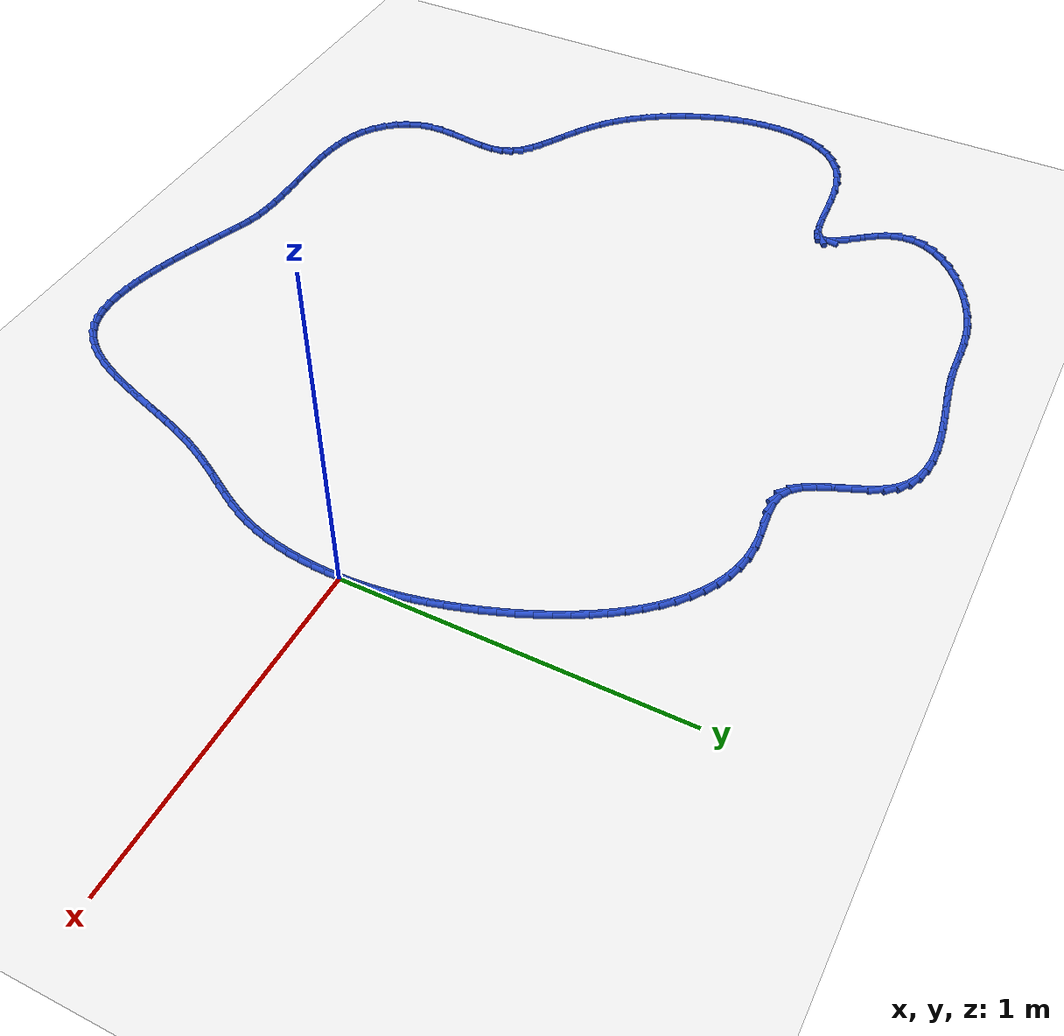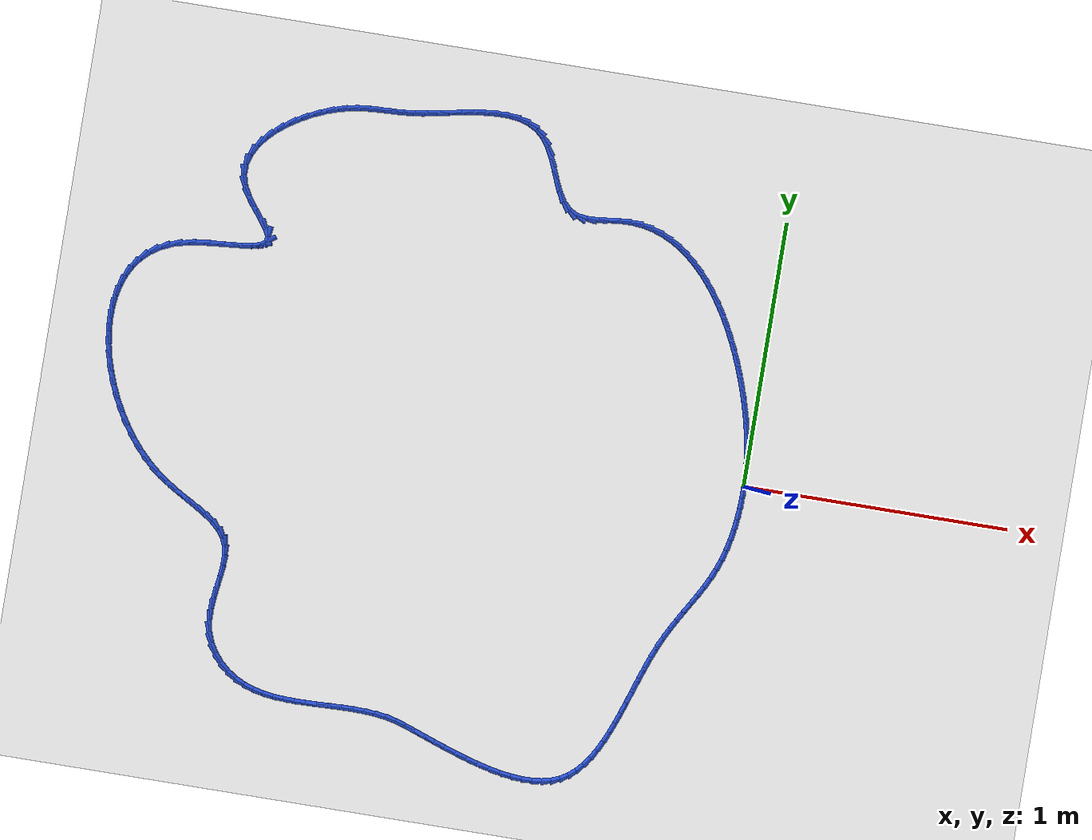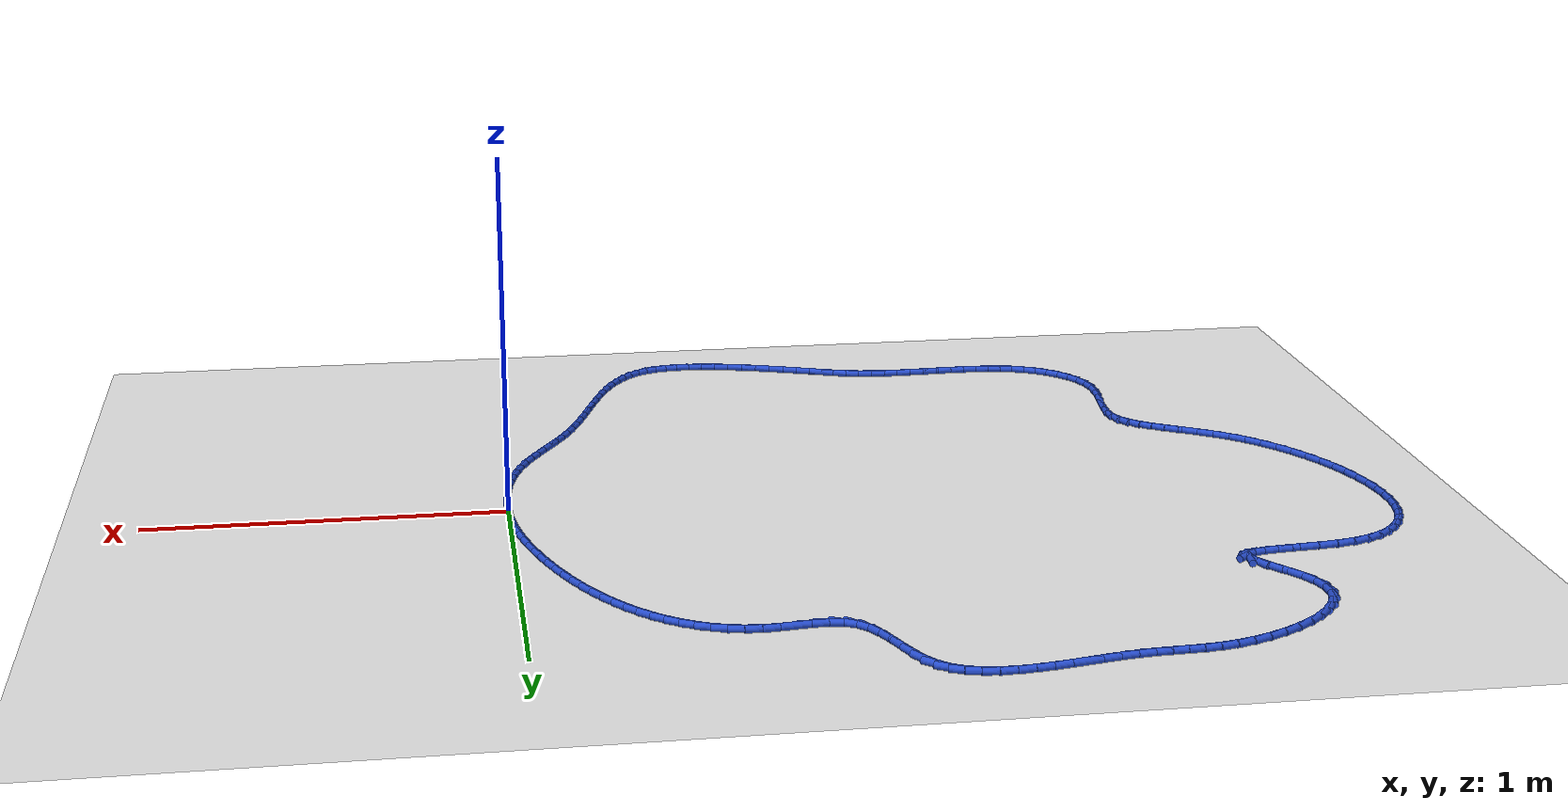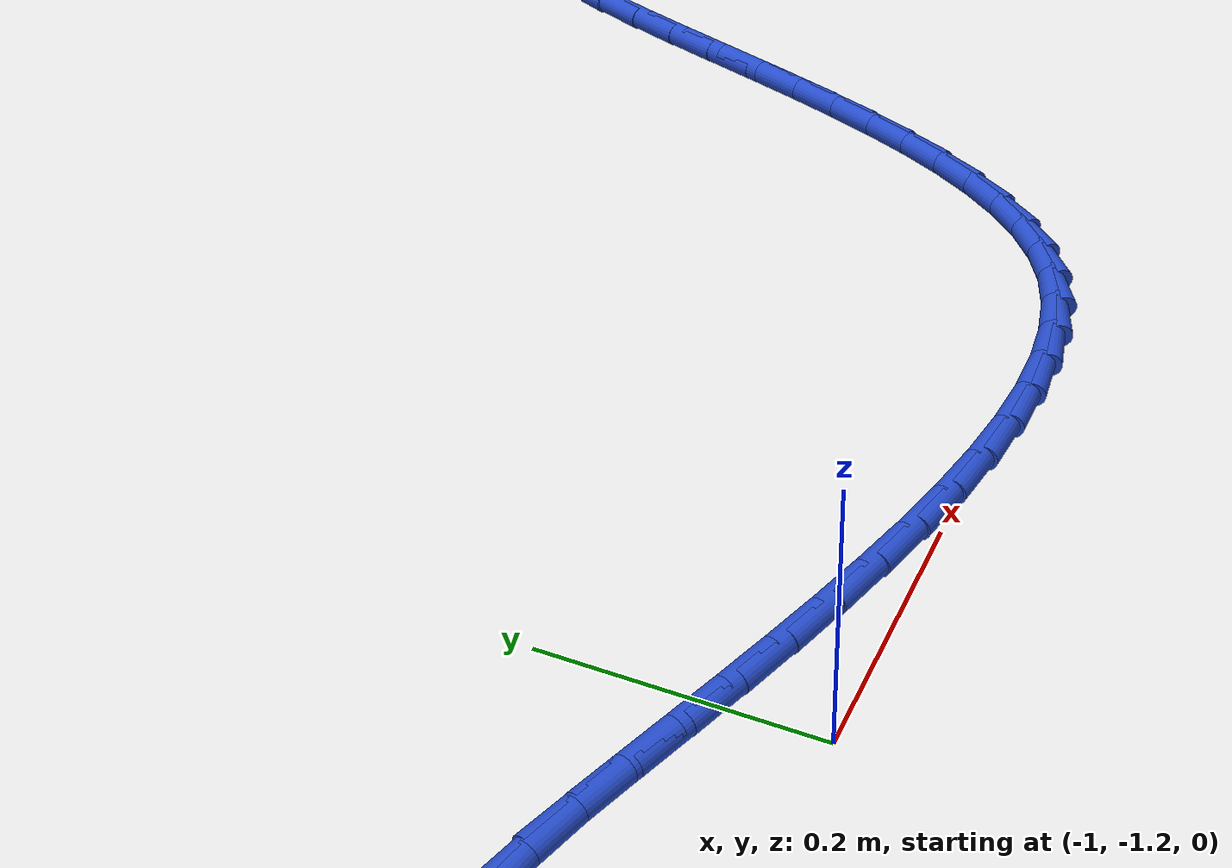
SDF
<sdf version="1.6">
 <world name="default">
  <light name="sun" type="directional">
   <pose>0 0 10 0 -0 0</pose>
   <diffuse>0.8 0.8 0.8 1</diffuse>
   <specular>0.2 0.2 0.2 1</specular>
   <attenuation>
    <range>1000</range>
    <constant>0.9</constant>
    <linear>0.01</linear>
    <quadratic>0.001</quadratic>
   </attenuation>
   <direction>-0.5 0.1 -0.9</direction>
  </light>
  <model name="ground_plane">
   <static>1</static>
   <link name="link">
    <collision name="collision">
     <geometry><plane><normal>0 0 1</normal><size>100 100</size></plane></geometry>
     <surface><friction><ode><mu>100</mu><mu2>50</mu2></ode></friction></surface>
    </collision>
    <visual name="visual">
     <cast_shadows>0</cast_shadows>
     <geometry><plane><normal>0 0 1</normal><size>100 100</size></plane></geometry>
     <material>
      <script><uri>file://media/materials/scripts/gazebo.material</uri><name>Gazebo/WhiteGlow</name></script>
     </material>
    </visual>
   </link>
  </model>
  <gravity>0 0 -9.8</gravity>
  <magnetic_field>6e-06 2.3e-05 -4.2e-05</magnetic_field>
  <atmosphere type="adiabatic"/>
  <physics name="default_physics" default="0" type="ode">
   <max_step_size>0.001</max_step_size>
   <real_time_factor>1</real_time_factor>
   <real_time_update_rate>1000</real_time_update_rate>
  </physics>
  <scene><ambient>0.4 0.4 0.4 1</ambient><background>0.7 0.7 0.7 1</background><shadows>1</shadows></scene>
  <spherical_coordinates>
   <surface_model>EARTH_WGS84</surface_model>
   <latitude_deg>0</latitude_deg>
   <longitude_deg>0</longitude_deg>
   <elevation>0</elevation>
   <heading_deg>0</heading_deg>
  </spherical_coordinates>
  <model name="line">
   <link name="link_0">
    <pose>1.3010426069826053e-17 5.551115123125783e-17 0.01 0 1.57 -1.5370923485594425</pose>
    <collision name="collision">
     <geometry><cylinder><radius>0.01</radius><length>0.08</length></cylinder></geometry>
    </collision>
    <visual name="visual">
     <material>
      <script><name>Gazebo/Blue</name><uri>file://media/materials/scripts/gazebo.material</uri></script>
     </material>
     <geometry><cylinder><radius>0.01</radius><length>0.08</length></cylinder></geometry>
    </visual>
   </link>
   <link name="link_1">
    <pose>-0.0013624470893869027 0.0404086172412097 0.01 0 1.57 -1.4985749646381814</pose>
    <collision name="collision">
     <geometry><cylinder><radius>0.01</radius><length>0.08</length></cylinder></geometry>
    </collision>
    <visual name="visual">
     <material>
      <script><name>Gazebo/Blue</name><uri>file://media/materials/scripts/gazebo.material</uri></script>
     </material>
     <geometry><cylinder><radius>0.01</radius><length>0.08</length></cylinder></geometry>
    </visual>
   </link>
   <link name="link_2">
    <pose>-0.004257589821566019 0.08042596500010882 0.01 0 1.57 -1.4602163294073707</pose>
    <collision name="collision">
     <geometry><cylinder><radius>0.01</radius><length>0.08</length></cylinder></geometry>
    </collision>
    <visual name="visual">
     <material>
      <script><name>Gazebo/Blue</name><uri>file://media/materials/scripts/gazebo.material</uri></script>
     </material>
     <geometry><cylinder><radius>0.01</radius><length>0.08</length></cylinder></geometry>
    </visual>
   </link>
   <link name="link_3">
    <pose>-0.00867618931539603 0.12022136002537331 0.01 0 1.57 -1.4226101593895641</pose>
    <collision name="collision">
     <geometry><cylinder><radius>0.01</radius><length>0.08</length></cylinder></geometry>
    </collision>
    <visual name="visual">
     <material>
      <script><name>Gazebo/Blue</name><uri>file://media/materials/scripts/gazebo.material</uri></script>
     </material>
     <geometry><cylinder><radius>0.01</radius><length>0.08</length></cylinder></geometry>
    </visual>
   </link>
   <link name="link_4">
    <pose>-0.014609006689735603 0.15996411906567878 0.01 0 1.57 -1.38631734847195</pose>
    <collision name="collision">
     <geometry><cylinder><radius>0.01</radius><length>0.08</length></cylinder></geometry>
    </collision>
    <visual name="visual">
     <material>
      <script><name>Gazebo/Blue</name><uri>file://media/materials/scripts/gazebo.material</uri></script>
     </material>
     <geometry><cylinder><radius>0.01</radius><length>0.08</length></cylinder></geometry>
    </visual>
   </link>
   <link name="link_5">
    <pose>-0.022046803063443435 0.19982355886970118 0.01 0 1.57 -1.3518347627467244</pose>
    <collision name="collision">
     <geometry><cylinder><radius>0.01</radius><length>0.08</length></cylinder></geometry>
    </collision>
    <visual name="visual">
     <material>
      <script><name>Gazebo/Blue</name><uri>file://media/materials/scripts/gazebo.material</uri></script>
     </material>
     <geometry><cylinder><radius>0.01</radius><length>0.08</length></cylinder></geometry>
    </visual>
   </link>
   <link name="link_6">
    <pose>-0.030980339555378204 0.2399689961861161 0.01 0 1.57 -1.3195720538327067</pose>
    <collision name="collision">
     <geometry><cylinder><radius>0.01</radius><length>0.08</length></cylinder></geometry>
    </collision>
    <visual name="visual">
     <material>
      <script><name>Gazebo/Blue</name><uri>file://media/materials/scripts/gazebo.material</uri></script>
     </material>
     <geometry><cylinder><radius>0.01</radius><length>0.08</length></cylinder></geometry>
    </visual>
   </link>
   <link name="link_7">
    <pose>-0.04140037728439858 0.28056974776359944 0.01 0 1.57 -1.2898385142903392</pose>
    <collision name="collision">
     <geometry><cylinder><radius>0.01</radius><length>0.08</length></cylinder></geometry>
    </collision>
    <visual name="visual">
     <material>
      <script><name>Gazebo/Blue</name><uri>file://media/materials/scripts/gazebo.material</uri></script>
     </material>
     <geometry><cylinder><radius>0.01</radius><length>0.08</length></cylinder></geometry>
    </visual>
   </link>
   <link name="link_8">
    <pose>-0.05329767736936328 0.32179513035082685 0.01 0 1.57 -1.262341019789148</pose>
    <collision name="collision">
     <geometry><cylinder><radius>0.01</radius><length>0.08</length></cylinder></geometry>
    </collision>
    <visual name="visual">
     <material>
      <script><name>Gazebo/Blue</name><uri>file://media/materials/scripts/gazebo.material</uri></script>
     </material>
     <geometry><cylinder><radius>0.01</radius><length>0.08</length></cylinder></geometry>
    </visual>
   </link>
   <link name="link_9">
    <pose>-0.06666568605233641 0.3637504140920044 0.01 0 1.57 -1.234554410372701</pose>
    <collision name="collision">
     <geometry><cylinder><radius>0.01</radius><length>0.08</length></cylinder></geometry>
    </collision>
    <visual name="visual">
     <material>
      <script><name>Gazebo/Blue</name><uri>file://media/materials/scripts/gazebo.material</uri></script>
     </material>
     <geometry><cylinder><radius>0.01</radius><length>0.08</length></cylinder></geometry>
    </visual>
   </link>
   <link name="link_10">
    <pose>-0.08151109889715967 0.4062248411480968 0.01 0 1.57 -1.205336084382853</pose>
    <collision name="collision">
     <geometry><cylinder><radius>0.01</radius><length>0.08</length></cylinder></geometry>
    </collision>
    <visual name="visual">
     <material>
      <script><name>Gazebo/Blue</name><uri>file://media/materials/scripts/gazebo.material</uri></script>
     </material>
     <geometry><cylinder><radius>0.01</radius><length>0.08</length></cylinder></geometry>
    </visual>
   </link>
   <link name="link_11">
    <pose>-0.09784469095491612 0.44891034816155284 0.01 0 1.57 -1.1742590518513734</pose>
    <collision name="collision">
     <geometry><cylinder><radius>0.01</radius><length>0.08</length></cylinder></geometry>
    </collision>
    <visual name="visual">
     <material>
      <script><name>Gazebo/Blue</name><uri>file://media/materials/scripts/gazebo.material</uri></script>
     </material>
     <geometry><cylinder><radius>0.01</radius><length>0.08</length></cylinder></geometry>
    </visual>
   </link>
   <link name="link_12">
    <pose>-0.11567723841007929 0.4914988447407492 0.01 0 1.57 -1.1408729727830687</pose>
    <collision name="collision">
     <geometry><cylinder><radius>0.01</radius><length>0.08</length></cylinder></geometry>
    </collision>
    <visual name="visual">
     <material>
      <script><name>Gazebo/Blue</name><uri>file://media/materials/scripts/gazebo.material</uri></script>
     </material>
     <geometry><cylinder><radius>0.01</radius><length>0.08</length></cylinder></geometry>
    </visual>
   </link>
   <link name="link_13">
    <pose>-0.13501951744712282 0.5336822404940627 0.01 0 1.57 -1.1046885955054375</pose>
    <collision name="collision">
     <geometry><cylinder><radius>0.01</radius><length>0.08</length></cylinder></geometry>
    </collision>
    <visual name="visual">
     <material>
      <script><name>Gazebo/Blue</name><uri>file://media/materials/scripts/gazebo.material</uri></script>
     </material>
     <geometry><cylinder><radius>0.01</radius><length>0.08</length></cylinder></geometry>
    </visual>
   </link>
   <link name="link_14">
    <pose>-0.15588230425052008 0.5751524450298697 0.01 0 1.57 -1.0651641285247224</pose>
    <collision name="collision">
     <geometry><cylinder><radius>0.01</radius><length>0.08</length></cylinder></geometry>
    </collision>
    <visual name="visual">
     <material>
      <script><name>Gazebo/Blue</name><uri>file://media/materials/scripts/gazebo.material</uri></script>
     </material>
     <geometry><cylinder><radius>0.01</radius><length>0.08</length></cylinder></geometry>
    </visual>
   </link>
   <link name="link_15">
    <pose>-0.1782763750047448 0.6156013679565474 0.01 0 1.57 -1.0216936180983174</pose>
    <collision name="collision">
     <geometry><cylinder><radius>0.01</radius><length>0.08</length></cylinder></geometry>
    </collision>
    <visual name="visual">
     <material>
      <script><name>Gazebo/Blue</name><uri>file://media/materials/scripts/gazebo.material</uri></script>
     </material>
     <geometry><cylinder><radius>0.01</radius><length>0.08</length></cylinder></geometry>
    </visual>
   </link>
   <link name="link_16">
    <pose>-0.20221250589427053 0.6547209188824723 0.01 0 1.57 -0.9735987434966186</pose>
    <collision name="collision">
     <geometry><cylinder><radius>0.01</radius><length>0.08</length></cylinder></geometry>
    </collision>
    <visual name="visual">
     <material>
      <script><name>Gazebo/Blue</name><uri>file://media/materials/scripts/gazebo.material</uri></script>
     </material>
     <geometry><cylinder><radius>0.01</radius><length>0.08</length></cylinder></geometry>
    </visual>
   </link>
   <link name="link_17">
    <pose>-0.2277014731035708 0.6922030074160211 0.01 0 1.57 -0.9201270300878676</pose>
    <collision name="collision">
     <geometry><cylinder><radius>0.01</radius><length>0.08</length></cylinder></geometry>
    </collision>
    <visual name="visual">
     <material>
      <script><name>Gazebo/Blue</name><uri>file://media/materials/scripts/gazebo.material</uri></script>
     </material>
     <geometry><cylinder><radius>0.01</radius><length>0.08</length></cylinder></geometry>
    </visual>
   </link>
   <link name="link_18">
    <pose>-0.25475405281711916 0.7277395431655707 0.01 0 1.57 -0.8604617501178689</pose>
    <collision name="collision">
     <geometry><cylinder><radius>0.01</radius><length>0.08</length></cylinder></geometry>
    </collision>
    <visual name="visual">
     <material>
      <script><name>Gazebo/Blue</name><uri>file://media/materials/scripts/gazebo.material</uri></script>
     </material>
     <geometry><cylinder><radius>0.01</radius><length>0.08</length></cylinder></geometry>
    </visual>
   </link>
   <link name="link_19">
    <pose>-0.28338102121938913 0.7610224357394975 0.01 0 1.57 -0.7937517886758415</pose>
    <collision name="collision">
     <geometry><cylinder><radius>0.01</radius><length>0.08</length></cylinder></geometry>
    </collision>
    <visual name="visual">
     <material>
      <script><name>Gazebo/Blue</name><uri>file://media/materials/scripts/gazebo.material</uri></script>
     </material>
     <geometry><cylinder><radius>0.01</radius><length>0.08</length></cylinder></geometry>
    </visual>
   </link>
   <link name="link_20">
    <pose>-0.3135931544948544 0.7917435947461786 0.01 0 1.57 -0.7191730166057886</pose>
    <collision name="collision">
     <geometry><cylinder><radius>0.01</radius><length>0.08</length></cylinder></geometry>
    </collision>
    <visual name="visual">
     <material>
      <script><name>Gazebo/Blue</name><uri>file://media/materials/scripts/gazebo.material</uri></script>
     </material>
     <geometry><cylinder><radius>0.01</radius><length>0.08</length></cylinder></geometry>
    </visual>
   </link>
   <link name="link_21">
    <pose>-0.34540122882798846 0.8195949297939904 0.01 0 1.57 -0.6360344900183127</pose>
    <collision name="collision">
     <geometry><cylinder><radius>0.01</radius><length>0.08</length></cylinder></geometry>
    </collision>
    <visual name="visual">
     <material>
      <script><name>Gazebo/Blue</name><uri>file://media/materials/scripts/gazebo.material</uri></script>
     </material>
     <geometry><cylinder><radius>0.01</radius><length>0.08</length></cylinder></geometry>
    </visual>
   </link>
   <link name="link_22">
    <pose>-0.3788160204032648 0.8442683504913097 0.01 0 1.57 -0.5439391399053539</pose>
    <collision name="collision">
     <geometry><cylinder><radius>0.01</radius><length>0.08</length></cylinder></geometry>
    </collision>
    <visual name="visual">
     <material>
      <script><name>Gazebo/Blue</name><uri>file://media/materials/scripts/gazebo.material</uri></script>
     </material>
     <geometry><cylinder><radius>0.01</radius><length>0.08</length></cylinder></geometry>
    </visual>
   </link>
   <link name="link_23">
    <pose>-0.41384830540515705 0.8654557664465133 0.01 0 1.57 -0.4429932710964172</pose>
    <collision name="collision">
     <geometry><cylinder><radius>0.01</radius><length>0.08</length></cylinder></geometry>
    </collision>
    <visual name="visual">
     <material>
      <script><name>Gazebo/Blue</name><uri>file://media/materials/scripts/gazebo.material</uri></script>
     </material>
     <geometry><cylinder><radius>0.01</radius><length>0.08</length></cylinder></geometry>
    </visual>
   </link>
   <link name="link_24">
    <pose>-0.45050886001813883 0.882849087267978 0.01 0 1.57 -0.33402707513901675</pose>
    <collision name="collision">
     <geometry><cylinder><radius>0.01</radius><length>0.08</length></cylinder></geometry>
    </collision>
    <visual name="visual">
     <material>
      <script><name>Gazebo/Blue</name><uri>file://media/materials/scripts/gazebo.material</uri></script>
     </material>
     <geometry><cylinder><radius>0.01</radius><length>0.08</length></cylinder></geometry>
    </visual>
   </link>
   <link name="link_25">
    <pose>-0.4888084604266835 0.8961402225640802 0.01 0 1.57 -0.2187455139513072</pose>
    <collision name="collision">
     <geometry><cylinder><radius>0.01</radius><length>0.08</length></cylinder></geometry>
    </collision>
    <visual name="visual">
     <material>
      <script><name>Gazebo/Blue</name><uri>file://media/materials/scripts/gazebo.material</uri></script>
     </material>
     <geometry><cylinder><radius>0.01</radius><length>0.08</length></cylinder></geometry>
    </visual>
   </link>
   <link name="link_26">
    <pose>-0.528757882815265 0.9050210819431972 0.01 0 1.57 -0.09970413066238601</pose>
    <collision name="collision">
     <geometry><cylinder><radius>0.01</radius><length>0.08</length></cylinder></geometry>
    </collision>
    <visual name="visual">
     <material>
      <script><name>Gazebo/Blue</name><uri>file://media/materials/scripts/gazebo.material</uri></script>
     </material>
     <geometry><cylinder><radius>0.01</radius><length>0.08</length></cylinder></geometry>
    </visual>
   </link>
   <link name="link_27">
    <pose>-0.5703679033683563 0.909183575013705 0.01 0 1.57 0.019249252064882278</pose>
    <collision name="collision">
     <geometry><cylinder><radius>0.01</radius><length>0.08</length></cylinder></geometry>
    </collision>
    <visual name="visual">
     <material>
      <script><name>Gazebo/Blue</name><uri>file://media/materials/scripts/gazebo.material</uri></script>
     </material>
     <geometry><cylinder><radius>0.01</radius><length>0.08</length></cylinder></geometry>
    </visual>
   </link>
   <link name="link_28">
    <pose>-0.6136354272823243 0.9083506046559225 0.01 0 1.57 0.10321474653686463</pose>
    <collision name="collision">
     <geometry><cylinder><radius>0.01</radius><length>0.08</length></cylinder></geometry>
    </collision>
    <visual name="visual">
     <material>
      <script><name>Gazebo/Blue</name><uri>file://media/materials/scripts/gazebo.material</uri></script>
     </material>
     <geometry><cylinder><radius>0.01</radius><length>0.08</length></cylinder></geometry>
    </visual>
   </link>
   <link name="link_29">
    <pose>-0.6578757467527033 0.9037680666999813 0.01 0 1.57 0.11206720125371548</pose>
    <collision name="collision">
     <geometry><cylinder><radius>0.01</radius><length>0.08</length></cylinder></geometry>
    </collision>
    <visual name="visual">
     <material>
      <script><name>Gazebo/Blue</name><uri>file://media/materials/scripts/gazebo.material</uri></script>
     </material>
     <geometry><cylinder><radius>0.01</radius><length>0.08</length></cylinder></geometry>
    </visual>
   </link>
   <link name="link_30">
    <pose>-0.7014262181568772 0.8988669522640895 0.01 0 1.57 0.03937064640493241</pose>
    <collision name="collision">
     <geometry><cylinder><radius>0.01</radius><length>0.08</length></cylinder></geometry>
    </collision>
    <visual name="visual">
     <material>
      <script><name>Gazebo/Blue</name><uri>file://media/materials/scripts/gazebo.material</uri></script>
     </material>
     <geometry><cylinder><radius>0.01</radius><length>0.08</length></cylinder></geometry>
    </visual>
   </link>
   <link name="link_31">
    <pose>-0.7425486307655478 0.8972470992615955 0.01 0 1.57 -0.14141432449012736</pose>
    <collision name="collision">
     <geometry><cylinder><radius>0.01</radius><length>0.08</length></cylinder></geometry>
    </collision>
    <visual name="visual">
     <material>
      <script><name>Gazebo/Blue</name><uri>file://media/materials/scripts/gazebo.material</uri></script>
     </material>
     <geometry><cylinder><radius>0.01</radius><length>0.08</length></cylinder></geometry>
    </visual>
   </link>
   <link name="link_32">
    <pose>-0.7795047738494155 0.9025083456058478 0.01 0 1.57 -0.46421868196721244</pose>
    <collision name="collision">
     <geometry><cylinder><radius>0.01</radius><length>0.08</length></cylinder></geometry>
    </collision>
    <visual name="visual">
     <material>
      <script><name>Gazebo/Blue</name><uri>file://media/materials/scripts/gazebo.material</uri></script>
     </material>
     <geometry><cylinder><radius>0.01</radius><length>0.08</length></cylinder></geometry>
    </visual>
   </link>
   <link name="link_33">
    <pose>-0.8106366461813062 0.9180965113349139 0.01 0 1.57 -0.8031513562574989</pose>
    <collision name="collision">
     <geometry><cylinder><radius>0.01</radius><length>0.08</length></cylinder></geometry>
    </collision>
    <visual name="visual">
     <material>
      <script><name>Gazebo/Blue</name><uri>file://media/materials/scripts/gazebo.material</uri></script>
     </material>
     <geometry><cylinder><radius>0.01</radius><length>0.08</length></cylinder></geometry>
    </visual>
   </link>
   <link name="link_34">
    <pose>-0.835928924039177 0.9443031555525615 0.01 0 1.57 -1.0201830672126324</pose>
    <collision name="collision">
     <geometry><cylinder><radius>0.01</radius><length>0.08</length></cylinder></geometry>
    </collision>
    <visual name="visual">
     <material>
      <script><name>Gazebo/Blue</name><uri>file://media/materials/scripts/gazebo.material</uri></script>
     </material>
     <geometry><cylinder><radius>0.01</radius><length>0.08</length></cylinder></geometry>
    </visual>
   </link>
   <link name="link_35">
    <pose>-0.8569039394316923 0.9784672387017579 0.01 0 1.57 -1.1367309435065938</pose>
    <collision name="collision">
     <geometry><cylinder><radius>0.01</radius><length>0.08</length></cylinder></geometry>
    </collision>
    <visual name="visual">
     <material>
      <script><name>Gazebo/Blue</name><uri>file://media/materials/scripts/gazebo.material</uri></script>
     </material>
     <geometry><cylinder><radius>0.01</radius><length>0.08</length></cylinder></geometry>
    </visual>
   </link>
   <link name="link_36">
    <pose>-0.8751432007690795 1.017814091002193 0.01 0 1.57 -1.182406942803605</pose>
    <collision name="collision">
     <geometry><cylinder><radius>0.01</radius><length>0.08</length></cylinder></geometry>
    </collision>
    <visual name="visual">
     <material>
      <script><name>Gazebo/Blue</name><uri>file://media/materials/scripts/gazebo.material</uri></script>
     </material>
     <geometry><cylinder><radius>0.01</radius><length>0.08</length></cylinder></geometry>
    </visual>
   </link>
   <link name="link_37">
    <pose>-0.8922282164615659 1.059569042673556 0.01 0 1.57 -1.1705185886554141</pose>
    <collision name="collision">
     <geometry><cylinder><radius>0.01</radius><length>0.08</length></cylinder></geometry>
    </collision>
    <visual name="visual">
     <material>
      <script><name>Gazebo/Blue</name><uri>file://media/materials/scripts/gazebo.material</uri></script>
     </material>
     <geometry><cylinder><radius>0.01</radius><length>0.08</length></cylinder></geometry>
    </visual>
   </link>
   <link name="link_38">
    <pose>-0.9097404949193789 1.1009574239355358 0.01 0 1.57 -1.0988694147319424</pose>
    <collision name="collision">
     <geometry><cylinder><radius>0.01</radius><length>0.08</length></cylinder></geometry>
    </collision>
    <visual name="visual">
     <material>
      <script><name>Gazebo/Blue</name><uri>file://media/materials/scripts/gazebo.material</uri></script>
     </material>
     <geometry><cylinder><radius>0.01</radius><length>0.08</length></cylinder></geometry>
    </visual>
   </link>
   <link name="link_39">
    <pose>-0.9292615445527463 1.1392045650078229 0.01 0 1.57 -0.9502490682633953</pose>
    <collision name="collision">
     <geometry><cylinder><radius>0.01</radius><length>0.08</length></cylinder></geometry>
    </collision>
    <visual name="visual">
     <material>
      <script><name>Gazebo/Blue</name><uri>file://media/materials/scripts/gazebo.material</uri></script>
     </material>
     <geometry><cylinder><radius>0.01</radius><length>0.08</length></cylinder></geometry>
    </visual>
   </link>
   <link name="link_40">
    <pose>-0.9523714994397455 1.1715381410669619 0.01 0 1.57 -0.7252552684759902</pose>
    <collision name="collision">
     <geometry><cylinder><radius>0.01</radius><length>0.08</length></cylinder></geometry>
    </collision>
    <visual name="visual">
     <material>
      <script><name>Gazebo/Blue</name><uri>file://media/materials/scripts/gazebo.material</uri></script>
     </material>
     <geometry><cylinder><radius>0.01</radius><length>0.08</length></cylinder></geometry>
    </visual>
   </link>
   <link name="link_41">
    <pose>-0.9801031539012923 1.196119726795475 0.01 0 1.57 -0.4966651508162846</pose>
    <collision name="collision">
     <geometry><cylinder><radius>0.01</radius><length>0.08</length></cylinder></geometry>
    </collision>
    <visual name="visual">
     <material>
      <script><name>Gazebo/Blue</name><uri>file://media/materials/scripts/gazebo.material</uri></script>
     </material>
     <geometry><cylinder><radius>0.01</radius><length>0.08</length></cylinder></geometry>
    </visual>
   </link>
   <link name="link_42">
    <pose>-1.0121089011509494 1.2134662089016306 0.01 0 1.57 -0.298592541449822</pose>
    <collision name="collision">
     <geometry><cylinder><radius>0.01</radius><length>0.08</length></cylinder></geometry>
    </collision>
    <visual name="visual">
     <material>
      <script><name>Gazebo/Blue</name><uri>file://media/materials/scripts/gazebo.material</uri></script>
     </material>
     <geometry><cylinder><radius>0.01</radius><length>0.08</length></cylinder></geometry>
    </visual>
   </link>
   <link name="link_43">
    <pose>-1.0478268947100895 1.2244600209776524 0.01 0 1.57 -0.14116448190820052</pose>
    <collision name="collision">
     <geometry><cylinder><radius>0.01</radius><length>0.08</length></cylinder></geometry>
    </collision>
    <visual name="visual">
     <material>
      <script><name>Gazebo/Blue</name><uri>file://media/materials/scripts/gazebo.material</uri></script>
     </material>
     <geometry><cylinder><radius>0.01</radius><length>0.08</length></cylinder></geometry>
    </visual>
   </link>
   <link name="link_44">
    <pose>-1.0866952881000869 1.2299835966157648 0.01 0 1.57 -0.0225683266223665</pose>
    <collision name="collision">
     <geometry><cylinder><radius>0.01</radius><length>0.08</length></cylinder></geometry>
    </collision>
    <visual name="visual">
     <material>
      <script><name>Gazebo/Blue</name><uri>file://media/materials/scripts/gazebo.material</uri></script>
     </material>
     <geometry><cylinder><radius>0.01</radius><length>0.08</length></cylinder></geometry>
    </visual>
   </link>
   <link name="link_45">
    <pose>-1.1281522348423132 1.2309193694081921 0.01 0 1.57 0.06360689847266744</pose>
    <collision name="collision">
     <geometry><cylinder><radius>0.01</radius><length>0.08</length></cylinder></geometry>
    </collision>
    <visual name="visual">
     <material>
      <script><name>Gazebo/Blue</name><uri>file://media/materials/scripts/gazebo.material</uri></script>
     </material>
     <geometry><cylinder><radius>0.01</radius><length>0.08</length></cylinder></geometry>
    </visual>
   </link>
   <link name="link_46">
    <pose>-1.1716358884581435 1.228149772947159 0.01 0 1.57 0.12378470963879804</pose>
    <collision name="collision">
     <geometry><cylinder><radius>0.01</radius><length>0.08</length></cylinder></geometry>
    </collision>
    <visual name="visual">
     <material>
      <script><name>Gazebo/Blue</name><uri>file://media/materials/scripts/gazebo.material</uri></script>
     </material>
     <geometry><cylinder><radius>0.01</radius><length>0.08</length></cylinder></geometry>
    </visual>
   </link>
   <link name="link_47">
    <pose>-1.2165844024689498 1.2225572408248895 0.01 0 1.57 0.16283719805359792</pose>
    <collision name="collision">
     <geometry><cylinder><radius>0.01</radius><length>0.08</length></cylinder></geometry>
    </collision>
    <visual name="visual">
     <material>
      <script><name>Gazebo/Blue</name><uri>file://media/materials/scripts/gazebo.material</uri></script>
     </material>
     <geometry><cylinder><radius>0.01</radius><length>0.08</length></cylinder></geometry>
    </visual>
   </link>
   <link name="link_48">
    <pose>-1.262435930396106 1.2150242066336077 0.01 0 1.57 0.18388304422452323</pose>
    <collision name="collision">
     <geometry><cylinder><radius>0.01</radius><length>0.08</length></cylinder></geometry>
    </collision>
    <visual name="visual">
     <material>
      <script><name>Gazebo/Blue</name><uri>file://media/materials/scripts/gazebo.material</uri></script>
     </material>
     <geometry><cylinder><radius>0.01</radius><length>0.08</length></cylinder></geometry>
    </visual>
   </link>
   <link name="link_49">
    <pose>-1.3086286257609843 1.2064331039655383 0.01 0 1.57 0.18843482636762715</pose>
    <collision name="collision">
     <geometry><cylinder><radius>0.01</radius><length>0.08</length></cylinder></geometry>
    </collision>
    <visual name="visual">
     <material>
      <script><name>Gazebo/Blue</name><uri>file://media/materials/scripts/gazebo.material</uri></script>
     </material>
     <geometry><cylinder><radius>0.01</radius><length>0.08</length></cylinder></geometry>
    </visual>
   </link>
   <link name="link_50">
    <pose>-1.3546006420849592 1.1976663664129055 0.01 0 1.57 0.17650269396958684</pose>
    <collision name="collision">
     <geometry><cylinder><radius>0.01</radius><length>0.08</length></cylinder></geometry>
    </collision>
    <visual name="visual">
     <material>
      <script><name>Gazebo/Blue</name><uri>file://media/materials/scripts/gazebo.material</uri></script>
     </material>
     <geometry><cylinder><radius>0.01</radius><length>0.08</length></cylinder></geometry>
    </visual>
   </link>
   <link name="link_51">
    <pose>-1.3997901328894038 1.1896064275679337 0.01 0 1.57 0.14652334351355203</pose>
    <collision name="collision">
     <geometry><cylinder><radius>0.01</radius><length>0.08</length></cylinder></geometry>
    </collision>
    <visual name="visual">
     <material>
      <script><name>Gazebo/Blue</name><uri>file://media/materials/scripts/gazebo.material</uri></script>
     </material>
     <geometry><cylinder><radius>0.01</radius><length>0.08</length></cylinder></geometry>
    </visual>
   </link>
   <link name="link_52">
    <pose>-1.44363525169569 1.1831357210228468 0.01 0 1.57 0.09819264468933056</pose>
    <collision name="collision">
     <geometry><cylinder><radius>0.01</radius><length>0.08</length></cylinder></geometry>
    </collision>
    <visual name="visual">
     <material>
      <script><name>Gazebo/Blue</name><uri>file://media/materials/scripts/gazebo.material</uri></script>
     </material>
     <geometry><cylinder><radius>0.01</radius><length>0.08</length></cylinder></geometry>
    </visual>
   </link>
   <link name="link_53">
    <pose>-1.4856597609849351 1.1789959096823739 0.01 0 1.57 0.05751145413509935</pose>
    <collision name="collision">
     <geometry><cylinder><radius>0.01</radius><length>0.08</length></cylinder></geometry>
    </collision>
    <visual name="visual">
     <material>
      <script><name>Gazebo/Blue</name><uri>file://media/materials/scripts/gazebo.material</uri></script>
     </material>
     <geometry><cylinder><radius>0.01</radius><length>0.08</length></cylinder></geometry>
    </visual>
   </link>
   <link name="link_54">
    <pose>-1.5261563213933664 1.176664322411486 0.01 0 1.57 0.043182065501372</pose>
    <collision name="collision">
     <geometry><cylinder><radius>0.01</radius><length>0.08</length></cylinder></geometry>
    </collision>
    <visual name="visual">
     <material>
      <script><name>Gazebo/Blue</name><uri>file://media/materials/scripts/gazebo.material</uri></script>
     </material>
     <geometry><cylinder><radius>0.01</radius><length>0.08</length></cylinder></geometry>
    </visual>
   </link>
   <link name="link_55">
    <pose>-1.5658238069753592 1.1749503329649094 0.01 0 1.57 0.057927254093104</pose>
    <collision name="collision">
     <geometry><cylinder><radius>0.01</radius><length>0.08</length></cylinder></geometry>
    </collision>
    <visual name="visual">
     <material>
      <script><name>Gazebo/Blue</name><uri>file://media/materials/scripts/gazebo.material</uri></script>
     </material>
     <geometry><cylinder><radius>0.01</radius><length>0.08</length></cylinder></geometry>
    </visual>
   </link>
   <link name="link_56">
    <pose>-1.6053647691853823 1.1726572681819398 0.01 0 1.57 0.10107804924206619</pose>
    <collision name="collision">
     <geometry><cylinder><radius>0.01</radius><length>0.08</length></cylinder></geometry>
    </collision>
    <visual name="visual">
     <material>
      <script><name>Gazebo/Blue</name><uri>file://media/materials/scripts/gazebo.material</uri></script>
     </material>
     <geometry><cylinder><radius>0.01</radius><length>0.08</length></cylinder></geometry>
    </visual>
   </link>
   <link name="link_57">
    <pose>-1.6454817594779065 1.1685884549018741 0.01 0 1.57 0.1684837900494039</pose>
    <collision name="collision">
     <geometry><cylinder><radius>0.01</radius><length>0.08</length></cylinder></geometry>
    </collision>
    <visual name="visual">
     <material>
      <script><name>Gazebo/Blue</name><uri>file://media/materials/scripts/gazebo.material</uri></script>
     </material>
     <geometry><cylinder><radius>0.01</radius><length>0.08</length></cylinder></geometry>
    </visual>
   </link>
   <link name="link_58">
    <pose>-1.6868773293074004 1.1615472199640064 0.01 0 1.57 0.252200047519293</pose>
    <collision name="collision">
     <geometry><cylinder><radius>0.01</radius><length>0.08</length></cylinder></geometry>
    </collision>
    <visual name="visual">
     <material>
      <script><name>Gazebo/Blue</name><uri>file://media/materials/scripts/gazebo.material</uri></script>
     </material>
     <geometry><cylinder><radius>0.01</radius><length>0.08</length></cylinder></geometry>
    </visual>
   </link>
   <link name="link_59">
    <pose>-1.730191828924542 1.1503856481204742 0.01 0 1.57 0.33511541404091305</pose>
    <collision name="collision">
     <geometry><cylinder><radius>0.01</radius><length>0.08</length></cylinder></geometry>
    </collision>
    <visual name="visual">
     <material>
      <script><name>Gazebo/Blue</name><uri>file://media/materials/scripts/gazebo.material</uri></script>
     </material>
     <geometry><cylinder><radius>0.01</radius><length>0.08</length></cylinder></geometry>
    </visual>
   </link>
   <link name="link_60">
    <pose>-1.7750228359813705 1.134773226558997 0.01 0 1.57 0.41228883957674495</pose>
    <collision name="collision">
     <geometry><cylinder><radius>0.01</radius><length>0.08</length></cylinder></geometry>
    </collision>
    <visual name="visual">
     <material>
      <script><name>Gazebo/Blue</name><uri>file://media/materials/scripts/gazebo.material</uri></script>
     </material>
     <geometry><cylinder><radius>0.01</radius><length>0.08</length></cylinder></geometry>
    </visual>
   </link>
   <link name="link_61">
    <pose>-1.820103726305783 1.115056867897165 0.01 0 1.57 0.4893554556167667</pose>
    <collision name="collision">
     <geometry><cylinder><radius>0.01</radius><length>0.08</length></cylinder></geometry>
    </collision>
    <visual name="visual">
     <material>
      <script><name>Gazebo/Blue</name><uri>file://media/materials/scripts/gazebo.material</uri></script>
     </material>
     <geometry><cylinder><radius>0.01</radius><length>0.08</length></cylinder></geometry>
    </visual>
   </link>
   <link name="link_62">
    <pose>-1.864141784131216 1.0916039372777793 0.01 0 1.57 0.571564491749729</pose>
    <collision name="collision">
     <geometry><cylinder><radius>0.01</radius><length>0.08</length></cylinder></geometry>
    </collision>
    <visual name="visual">
     <material>
      <script><name>Gazebo/Blue</name><uri>file://media/materials/scripts/gazebo.material</uri></script>
     </material>
     <geometry><cylinder><radius>0.01</radius><length>0.08</length></cylinder></geometry>
    </visual>
   </link>
   <link name="link_63">
    <pose>-1.9058442936911044 1.06478179984364 0.01 0 1.57 0.6644816196765047</pose>
    <collision name="collision">
     <geometry><cylinder><radius>0.01</radius><length>0.08</length></cylinder></geometry>
    </collision>
    <visual name="visual">
     <material>
      <script><name>Gazebo/Blue</name><uri>file://media/materials/scripts/gazebo.material</uri></script>
     </material>
     <geometry><cylinder><radius>0.01</radius><length>0.08</length></cylinder></geometry>
    </visual>
   </link>
   <link name="link_64">
    <pose>-1.9439185392188851 1.0349578207375465 0.01 0 1.57 0.7748088341033493</pose>
    <collision name="collision">
     <geometry><cylinder><radius>0.01</radius><length>0.08</length></cylinder></geometry>
    </collision>
    <visual name="visual">
     <material>
      <script><name>Gazebo/Blue</name><uri>file://media/materials/scripts/gazebo.material</uri></script>
     </material>
     <geometry><cylinder><radius>0.01</radius><length>0.08</length></cylinder></geometry>
    </visual>
   </link>
   <link name="link_65">
    <pose>-1.9770718049479925 1.0024993651023004 0.01 0 1.57 0.910996080590213</pose>
    <collision name="collision">
     <geometry><cylinder><radius>0.01</radius><length>0.08</length></cylinder></geometry>
    </collision>
    <visual name="visual">
     <material>
      <script><name>Gazebo/Blue</name><uri>file://media/materials/scripts/gazebo.material</uri></script>
     </material>
     <geometry><cylinder><radius>0.01</radius><length>0.08</length></cylinder></geometry>
    </visual>
   </link>
   <link name="link_66">
    <pose>-2.0040113751118627 0.9677737980807014 0.01 0 1.57 1.0829743940209737</pose>
    <collision name="collision">
     <geometry><cylinder><radius>0.01</radius><length>0.08</length></cylinder></geometry>
    </collision>
    <visual name="visual">
     <material>
      <script><name>Gazebo/Blue</name><uri>file://media/materials/scripts/gazebo.material</uri></script>
     </material>
     <geometry><cylinder><radius>0.01</radius><length>0.08</length></cylinder></geometry>
    </visual>
   </link>
   <link name="link_67">
    <pose>-2.023444533943932 0.9311484848155497 0.01 0 1.57 1.2990061089863076</pose>
    <collision name="collision">
     <geometry><cylinder><radius>0.01</radius><length>0.08</length></cylinder></geometry>
    </collision>
    <visual name="visual">
     <material>
      <script><name>Gazebo/Blue</name><uri>file://media/materials/scripts/gazebo.material</uri></script>
     </material>
     <geometry><cylinder><radius>0.01</radius><length>0.08</length></cylinder></geometry>
    </visual>
   </link>
   <link name="link_68">
    <pose>-2.0340785656776355 0.8929907904496458 0.01 0 1.57 1.5570090138406496</pose>
    <collision name="collision">
     <geometry><cylinder><radius>0.01</radius><length>0.08</length></cylinder></geometry>
    </collision>
    <visual name="visual">
     <material>
      <script><name>Gazebo/Blue</name><uri>file://media/materials/scripts/gazebo.material</uri></script>
     </material>
     <geometry><cylinder><radius>0.01</radius><length>0.08</length></cylinder></geometry>
    </visual>
   </link>
   <link name="link_69">
    <pose>-2.034620754546409 0.8536680801257899 0.01 0 1.57 -1.3069392731303564</pose>
    <collision name="collision">
     <geometry><cylinder><radius>0.01</radius><length>0.08</length></cylinder></geometry>
    </collision>
    <visual name="visual">
     <material>
      <script><name>Gazebo/Blue</name><uri>file://media/materials/scripts/gazebo.material</uri></script>
     </material>
     <geometry><cylinder><radius>0.01</radius><length>0.08</length></cylinder></geometry>
    </visual>
   </link>
   <link name="link_70">
    <pose>-2.0237821685634185 0.8135483214166329 0.01 0 1.57 -1.0748596494038498</pose>
    <collision name="collision">
     <geometry><cylinder><radius>0.01</radius><length>0.08</length></cylinder></geometry>
    </collision>
    <visual name="visual">
     <material>
      <script><name>Gazebo/Blue</name><uri>file://media/materials/scripts/gazebo.material</uri></script>
     </material>
     <geometry><cylinder><radius>0.01</radius><length>0.08</length></cylinder></geometry>
    </visual>
   </link>
   <link name="link_71">
    <pose>-2.001991672067023 0.7732729787301851 0.01 0 1.57 -0.9510855397626315</pose>
    <collision name="collision">
     <geometry><cylinder><radius>0.01</radius><length>0.08</length></cylinder></geometry>
    </collision>
    <visual name="visual">
     <material>
      <script><name>Gazebo/Blue</name><uri>file://media/materials/scripts/gazebo.material</uri></script>
     </material>
     <geometry><cylinder><radius>0.01</radius><length>0.08</length></cylinder></geometry>
    </visual>
   </link>
   <link name="link_72">
    <pose>-1.974105963987081 0.7341884887290381 0.01 0 1.57 -0.9083521146899635</pose>
    <collision name="collision">
     <geometry><cylinder><radius>0.01</radius><length>0.08</length></cylinder></geometry>
    </collision>
    <visual name="visual">
     <material>
      <script><name>Gazebo/Blue</name><uri>file://media/materials/scripts/gazebo.material</uri></script>
     </material>
     <geometry><cylinder><radius>0.01</radius><length>0.08</length></cylinder></geometry>
    </visual>
   </link>
   <link name="link_73">
    <pose>-1.9456854939136063 0.6977533348741227 0.01 0 1.57 -0.9443511106208655</pose>
    <collision name="collision">
     <geometry><cylinder><radius>0.01</radius><length>0.08</length></cylinder></geometry>
    </collision>
    <visual name="visual">
     <material>
      <script><name>Gazebo/Blue</name><uri>file://media/materials/scripts/gazebo.material</uri></script>
     </material>
     <geometry><cylinder><radius>0.01</radius><length>0.08</length></cylinder></geometry>
    </visual>
   </link>
   <link name="link_74">
    <pose>-1.9222907114366148 0.6654260006263688 0.01 0 1.57 -1.1243900123114519</pose>
    <collision name="collision">
     <geometry><cylinder><radius>0.01</radius><length>0.08</length></cylinder></geometry>
    </collision>
    <visual name="visual">
     <material>
      <script><name>Gazebo/Blue</name><uri>file://media/materials/scripts/gazebo.material</uri></script>
     </material>
     <geometry><cylinder><radius>0.01</radius><length>0.08</length></cylinder></geometry>
    </visual>
   </link>
   <link name="link_75">
    <pose>-1.9094820661461227 0.638664969446707 0.01 0 1.57 1.4323308383723228</pose>
    <collision name="collision">
     <geometry><cylinder><radius>0.01</radius><length>0.08</length></cylinder></geometry>
    </collision>
    <visual name="visual">
     <material>
      <script><name>Gazebo/Blue</name><uri>file://media/materials/scripts/gazebo.material</uri></script>
     </material>
     <geometry><cylinder><radius>0.01</radius><length>0.08</length></cylinder></geometry>
    </visual>
   </link>
   <link name="link_76">
    <pose>-1.91226055762006 0.6187270649631366 0.01 0 1.57 0.6424432585882228</pose>
    <collision name="collision">
     <geometry><cylinder><radius>0.01</radius><length>0.08</length></cylinder></geometry>
    </collision>
    <visual name="visual">
     <material>
      <script><name>Gazebo/Blue</name><uri>file://media/materials/scripts/gazebo.material</uri></script>
     </material>
     <geometry><cylinder><radius>0.01</radius><length>0.08</length></cylinder></geometry>
    </visual>
   </link>
   <link name="link_77">
    <pose>-1.9305510872084979 0.6050393760669314 0.01 0 1.57 0.28190814599308156</pose>
    <collision name="collision">
     <geometry><cylinder><radius>0.01</radius><length>0.08</length></cylinder></geometry>
    </collision>
    <visual name="visual">
     <material>
      <script><name>Gazebo/Blue</name><uri>file://media/materials/scripts/gazebo.material</uri></script>
     </material>
     <geometry><cylinder><radius>0.01</radius><length>0.08</length></cylinder></geometry>
    </visual>
   </link>
   <link name="link_78">
    <pose>-1.9615745722751252 0.5960543112540417 0.01 0 1.57 0.14162906285425741</pose>
    <collision name="collision">
     <geometry><cylinder><radius>0.01</radius><length>0.08</length></cylinder></geometry>
    </collision>
    <visual name="visual">
     <material>
      <script><name>Gazebo/Blue</name><uri>file://media/materials/scripts/gazebo.material</uri></script>
     </material>
     <geometry><cylinder><radius>0.01</radius><length>0.08</length></cylinder></geometry>
    </visual>
   </link>
   <link name="link_79">
    <pose>-2.002526742037474 0.5902151996795726 0.01 0 1.57 0.08816789836341815</pose>
    <collision name="collision">
     <geometry><cylinder><radius>0.01</radius><length>0.08</length></cylinder></geometry>
    </collision>
    <visual name="visual">
     <material>
      <script><name>Gazebo/Blue</name><uri>file://media/materials/scripts/gazebo.material</uri></script>
     </material>
     <geometry><cylinder><radius>0.01</radius><length>0.08</length></cylinder></geometry>
    </visual>
   </link>
   <link name="link_80">
    <pose>-2.050603325713078 0.5859653704986288 0.01 0 1.57 0.08031315473913857</pose>
    <collision name="collision">
     <geometry><cylinder><radius>0.01</radius><length>0.08</length></cylinder></geometry>
    </collision>
    <visual name="visual">
     <material>
      <script><name>Gazebo/Blue</name><uri>file://media/materials/scripts/gazebo.material</uri></script>
     </material>
     <geometry><cylinder><radius>0.01</radius><length>0.08</length></cylinder></geometry>
    </visual>
   </link>
   <link name="link_81">
    <pose>-2.1030000525194694 0.5817481528663158 0.01 0 1.57 0.1060924591469396</pose>
    <collision name="collision">
     <geometry><cylinder><radius>0.01</radius><length>0.08</length></cylinder></geometry>
    </collision>
    <visual name="visual">
     <material>
      <script><name>Gazebo/Blue</name><uri>file://media/materials/scripts/gazebo.material</uri></script>
     </material>
     <geometry><cylinder><radius>0.01</radius><length>0.08</length></cylinder></geometry>
    </visual>
   </link>
   <link name="link_82">
    <pose>-2.156912651674183 0.5760068759377381 0.01 0 1.57 0.16609714538901912</pose>
    <collision name="collision">
     <geometry><cylinder><radius>0.01</radius><length>0.08</length></cylinder></geometry>
    </collision>
    <visual name="visual">
     <material>
      <script><name>Gazebo/Blue</name><uri>file://media/materials/scripts/gazebo.material</uri></script>
     </material>
     <geometry><cylinder><radius>0.01</radius><length>0.08</length></cylinder></geometry>
    </visual>
   </link>
   <link name="link_83">
    <pose>-2.2095368523947494 0.5671848688680012 0.01 0 1.57 0.27040608945299766</pose>
    <collision name="collision">
     <geometry><cylinder><radius>0.01</radius><length>0.08</length></cylinder></geometry>
    </collision>
    <visual name="visual">
     <material>
      <script><name>Gazebo/Blue</name><uri>file://media/materials/scripts/gazebo.material</uri></script>
     </material>
     <geometry><cylinder><radius>0.01</radius><length>0.08</length></cylinder></geometry>
    </visual>
   </link>
   <link name="link_84">
    <pose>-2.258075394941664 0.553730209173439 0.01 0 1.57 0.41984244460762843</pose>
    <collision name="collision">
     <geometry><cylinder><radius>0.01</radius><length>0.08</length></cylinder></geometry>
    </collision>
    <visual name="visual">
     <material>
      <script><name>Gazebo/Blue</name><uri>file://media/materials/scripts/gazebo.material</uri></script>
     </material>
     <geometry><cylinder><radius>0.01</radius><length>0.08</length></cylinder></geometry>
    </visual>
   </link>
   <link name="link_85">
    <pose>-2.300660886988296 0.5347207446336341 0.01 0 1.57 0.58461759404443</pose>
    <collision name="collision">
     <geometry><cylinder><radius>0.01</radius><length>0.08</length></cylinder></geometry>
    </collision>
    <visual name="visual">
     <material>
      <script><name>Gazebo/Blue</name><uri>file://media/materials/scripts/gazebo.material</uri></script>
     </material>
     <geometry><cylinder><radius>0.01</radius><length>0.08</length></cylinder></geometry>
    </visual>
   </link>
   <link name="link_86">
    <pose>-2.33727747960394 0.5104883157541514 0.01 0 1.57 0.7540507502458224</pose>
    <collision name="collision">
     <geometry><cylinder><radius>0.01</radius><length>0.08</length></cylinder></geometry>
    </collision>
    <visual name="visual">
     <material>
      <script><name>Gazebo/Blue</name><uri>file://media/materials/scripts/gazebo.material</uri></script>
     </material>
     <geometry><cylinder><radius>0.01</radius><length>0.08</length></cylinder></geometry>
    </visual>
   </link>
   <link name="link_87">
    <pose>-2.368128560069671 0.4815132449046287 0.01 0 1.57 0.9203818345682576</pose>
    <collision name="collision">
     <geometry><cylinder><radius>0.01</radius><length>0.08</length></cylinder></geometry>
    </collision>
    <visual name="visual">
     <material>
      <script><name>Gazebo/Blue</name><uri>file://media/materials/scripts/gazebo.material</uri></script>
     </material>
     <geometry><cylinder><radius>0.01</radius><length>0.08</length></cylinder></geometry>
    </visual>
   </link>
   <link name="link_88">
    <pose>-2.393417515666566 0.4482758544547048 0.01 0 1.57 1.0769240335240629</pose>
    <collision name="collision">
     <geometry><cylinder><radius>0.01</radius><length>0.08</length></cylinder></geometry>
    </collision>
    <visual name="visual">
     <material>
      <script><name>Gazebo/Blue</name><uri>file://media/materials/scripts/gazebo.material</uri></script>
     </material>
     <geometry><cylinder><radius>0.01</radius><length>0.08</length></cylinder></geometry>
    </visual>
   </link>
   <link name="link_89">
    <pose>-2.413347733675697 0.41125646677401795 0.01 0 1.57 1.2195597139332894</pose>
    <collision name="collision">
     <geometry><cylinder><radius>0.01</radius><length>0.08</length></cylinder></geometry>
    </collision>
    <visual name="visual">
     <material>
      <script><name>Gazebo/Blue</name><uri>file://media/materials/scripts/gazebo.material</uri></script>
     </material>
     <geometry><cylinder><radius>0.01</radius><length>0.08</length></cylinder></geometry>
    </visual>
   </link>
   <link name="link_90">
    <pose>-2.428122601378141 0.3709354042322073 0.01 0 1.57 1.3469272101276322</pose>
    <collision name="collision">
     <geometry><cylinder><radius>0.01</radius><length>0.08</length></cylinder></geometry>
    </collision>
    <visual name="visual">
     <material>
      <script><name>Gazebo/Blue</name><uri>file://media/materials/scripts/gazebo.material</uri></script>
     </material>
     <geometry><cylinder><radius>0.01</radius><length>0.08</length></cylinder></geometry>
    </visual>
   </link>
   <link name="link_91">
    <pose>-2.4379455060549717 0.3277929891989102 0.01 0 1.57 1.459691461118424</pose>
    <collision name="collision">
     <geometry><cylinder><radius>0.01</radius><length>0.08</length></cylinder></geometry>
    </collision>
    <visual name="visual">
     <material>
      <script><name>Gazebo/Blue</name><uri>file://media/materials/scripts/gazebo.material</uri></script>
     </material>
     <geometry><cylinder><radius>0.01</radius><length>0.08</length></cylinder></geometry>
    </visual>
   </link>
   <link name="link_92">
    <pose>-2.4430198349872634 0.28230954404376535 0.01 0 1.57 1.5596203228803498</pose>
    <collision name="collision">
     <geometry><cylinder><radius>0.01</radius><length>0.08</length></cylinder></geometry>
    </collision>
    <visual name="visual">
     <material>
      <script><name>Gazebo/Blue</name><uri>file://media/materials/scripts/gazebo.material</uri></script>
     </material>
     <geometry><cylinder><radius>0.01</radius><length>0.08</length></cylinder></geometry>
    </visual>
   </link>
   <link name="link_93">
    <pose>-2.443548975456092 0.2349653911364119 0.01 0 1.57 -1.4927061543497409</pose>
    <collision name="collision">
     <geometry><cylinder><radius>0.01</radius><length>0.08</length></cylinder></geometry>
    </collision>
    <visual name="visual">
     <material>
      <script><name>Gazebo/Blue</name><uri>file://media/materials/scripts/gazebo.material</uri></script>
     </material>
     <geometry><cylinder><radius>0.01</radius><length>0.08</length></cylinder></geometry>
    </visual>
   </link>
   <link name="link_94">
    <pose>-2.4397363147425315 0.18624085284648728 0.01 0 1.57 -1.4119222215359504</pose>
    <collision name="collision">
     <geometry><cylinder><radius>0.01</radius><length>0.08</length></cylinder></geometry>
    </collision>
    <visual name="visual">
     <material>
      <script><name>Gazebo/Blue</name><uri>file://media/materials/scripts/gazebo.material</uri></script>
     </material>
     <geometry><cylinder><radius>0.01</radius><length>0.08</length></cylinder></geometry>
    </visual>
   </link>
   <link name="link_95">
    <pose>-2.431785240127658 0.13661625154363036 0.01 0 1.57 -1.3376057440010736</pose>
    <collision name="collision">
     <geometry><cylinder><radius>0.01</radius><length>0.08</length></cylinder></geometry>
    </collision>
    <visual name="visual">
     <material>
      <script><name>Gazebo/Blue</name><uri>file://media/materials/scripts/gazebo.material</uri></script>
     </material>
     <geometry><cylinder><radius>0.01</radius><length>0.08</length></cylinder></geometry>
    </visual>
   </link>
   <link name="link_96">
    <pose>-2.4198991388925437 0.08657190959747951 0.01 0 1.57 -1.2679512747348227</pose>
    <collision name="collision">
     <geometry><cylinder><radius>0.01</radius><length>0.08</length></cylinder></geometry>
    </collision>
    <visual name="visual">
     <material>
      <script><name>Gazebo/Blue</name><uri>file://media/materials/scripts/gazebo.material</uri></script>
     </material>
     <geometry><cylinder><radius>0.01</radius><length>0.08</length></cylinder></geometry>
    </visual>
   </link>
   <link name="link_97">
    <pose>-2.404281398318266 0.036588149377673206 0.01 0 1.57 -1.2013426688589506</pose>
    <collision name="collision">
     <geometry><cylinder><radius>0.01</radius><length>0.08</length></cylinder></geometry>
    </collision>
    <visual name="visual">
     <material>
      <script><name>Gazebo/Blue</name><uri>file://media/materials/scripts/gazebo.material</uri></script>
     </material>
     <geometry><cylinder><radius>0.01</radius><length>0.08</length></cylinder></geometry>
    </visual>
   </link>
   <link name="link_98">
    <pose>-2.3851354056858987 -0.012854706746149108 0.01 0 1.57 -1.1363064461695538</pose>
    <collision name="collision">
     <geometry><cylinder><radius>0.01</radius><length>0.08</length></cylinder></geometry>
    </collision>
    <visual name="visual">
     <material>
      <script><name>Gazebo/Blue</name><uri>file://media/materials/scripts/gazebo.material</uri></script>
     </material>
     <geometry><cylinder><radius>0.01</radius><length>0.08</length></cylinder></geometry>
    </visual>
   </link>
   <link name="link_99">
    <pose>-2.3626645482765167 -0.06127633640435111 0.01 0 1.57 -1.071456774233871</pose>
    <collision name="collision">
     <geometry><cylinder><radius>0.01</radius><length>0.08</length></cylinder></geometry>
    </collision>
    <visual name="visual">
     <material>
      <script><name>Gazebo/Blue</name><uri>file://media/materials/scripts/gazebo.material</uri></script>
     </material>
     <geometry><cylinder><radius>0.01</radius><length>0.08</length></cylinder></geometry>
    </visual>
   </link>
   <link name="link_100">
    <pose>-2.3370722133711945 -0.10819641722729324 0.01 0 1.57 -1.0054402172559207</pose>
    <collision name="collision">
     <geometry><cylinder><radius>0.01</radius><length>0.08</length></cylinder></geometry>
    </collision>
    <visual name="visual">
     <material>
      <script><name>Gazebo/Blue</name><uri>file://media/materials/scripts/gazebo.material</uri></script>
     </material>
     <geometry><cylinder><radius>0.01</radius><length>0.08</length></cylinder></geometry>
    </visual>
   </link>
   <link name="link_101">
    <pose>-2.3085617882510063 -0.15313462684533716 0.01 0 1.57 -0.936884199473139</pose>
    <collision name="collision">
     <geometry><cylinder><radius>0.01</radius><length>0.08</length></cylinder></geometry>
    </collision>
    <visual name="visual">
     <material>
      <script><name>Gazebo/Blue</name><uri>file://media/materials/scripts/gazebo.material</uri></script>
     </material>
     <geometry><cylinder><radius>0.01</radius><length>0.08</length></cylinder></geometry>
    </visual>
   </link>
   <link name="link_102">
    <pose>-2.2773366601970286 -0.19561064288884442 0.01 0 1.57 -0.8643528493745478</pose>
    <collision name="collision">
     <geometry><cylinder><radius>0.01</radius><length>0.08</length></cylinder></geometry>
    </collision>
    <visual name="visual">
     <material>
      <script><name>Gazebo/Blue</name><uri>file://media/materials/scripts/gazebo.material</uri></script>
     </material>
     <geometry><cylinder><radius>0.01</radius><length>0.08</length></cylinder></geometry>
    </visual>
   </link>
   <link name="link_103">
    <pose>-2.2436002164903353 -0.23514414298817665 0.01 0 1.57 -0.7863168753013023</pose>
    <collision name="collision">
     <geometry><cylinder><radius>0.01</radius><length>0.08</length></cylinder></geometry>
    </collision>
    <visual name="visual">
     <material>
      <script><name>Gazebo/Blue</name><uri>file://media/materials/scripts/gazebo.material</uri></script>
     </material>
     <geometry><cylinder><radius>0.01</radius><length>0.08</length></cylinder></geometry>
    </visual>
   </link>
   <link name="link_104">
    <pose>-2.2075558444120005 -0.27125480477369535 0.01 0 1.57 -0.7012964988675874</pose>
    <collision name="collision">
     <geometry><cylinder><radius>0.01</radius><length>0.08</length></cylinder></geometry>
    </collision>
    <visual name="visual">
     <material>
      <script><name>Gazebo/Blue</name><uri>file://media/materials/scripts/gazebo.material</uri></script>
     </material>
     <geometry><cylinder><radius>0.01</radius><length>0.08</length></cylinder></geometry>
    </visual>
   </link>
   <link name="link_105">
    <pose>-2.169410834465066 -0.3034685366648414 0.01 0 1.57 -0.6194975023048076</pose>
    <collision name="collision">
     <geometry><cylinder><radius>0.01</radius><length>0.08</length></cylinder></geometry>
    </collision>
    <visual name="visual">
     <material>
      <script><name>Gazebo/Blue</name><uri>file://media/materials/scripts/gazebo.material</uri></script>
     </material>
     <geometry><cylinder><radius>0.01</radius><length>0.08</length></cylinder></geometry>
    </visual>
   </link>
   <link name="link_106">
    <pose>-2.1296801975776556 -0.33180246717597905 0.01 0 1.57 -0.5610306374395739</pose>
    <collision name="collision">
     <geometry><cylinder><radius>0.01</radius><length>0.08</length></cylinder></geometry>
    </collision>
    <visual name="visual">
     <material>
      <script><name>Gazebo/Blue</name><uri>file://media/materials/scripts/gazebo.material</uri></script>
     </material>
     <geometry><cylinder><radius>0.01</radius><length>0.08</length></cylinder></geometry>
    </visual>
   </link>
   <link name="link_107">
    <pose>-2.0894038172662768 -0.3571115891348825 0.01 0 1.57 -0.5289137648425014</pose>
    <collision name="collision">
     <geometry><cylinder><radius>0.01</radius><length>0.08</length></cylinder></geometry>
    </collision>
    <visual name="visual">
     <material>
      <script><name>Gazebo/Blue</name><uri>file://media/materials/scripts/gazebo.material</uri></script>
     </material>
     <geometry><cylinder><radius>0.01</radius><length>0.08</length></cylinder></geometry>
    </visual>
   </link>
   <link name="link_108">
    <pose>-2.0496728313261676 -0.38033271357055703 0.01 0 1.57 -0.5250956270011502</pose>
    <collision name="collision">
     <geometry><cylinder><radius>0.01</radius><length>0.08</length></cylinder></geometry>
    </collision>
    <visual name="visual">
     <material>
      <script><name>Gazebo/Blue</name><uri>file://media/materials/scripts/gazebo.material</uri></script>
     </material>
     <geometry><cylinder><radius>0.01</radius><length>0.08</length></cylinder></geometry>
    </visual>
   </link>
   <link name="link_109">
    <pose>-2.0115783775525644 -0.4024026515120082 0.01 0 1.57 -0.5535270539954007</pose>
    <collision name="collision">
     <geometry><cylinder><radius>0.01</radius><length>0.08</length></cylinder></geometry>
    </collision>
    <visual name="visual">
     <material>
      <script><name>Gazebo/Blue</name><uri>file://media/materials/scripts/gazebo.material</uri></script>
     </material>
     <geometry><cylinder><radius>0.01</radius><length>0.08</length></cylinder></geometry>
    </visual>
   </link>
   <link name="link_110">
    <pose>-1.9762115937407045 -0.42425821398824143 0.01 0 1.57 -0.6211667237246505</pose>
    <collision name="collision">
     <geometry><cylinder><radius>0.01</radius><length>0.08</length></cylinder></geometry>
    </collision>
    <visual name="visual">
     <material>
      <script><name>Gazebo/Blue</name><uri>file://media/materials/scripts/gazebo.material</uri></script>
     </material>
     <geometry><cylinder><radius>0.01</radius><length>0.08</length></cylinder></geometry>
    </visual>
   </link>
   <link name="link_111">
    <pose>-1.944663617685824 -0.44683621202826207 0.01 0 1.57 -0.738243505898842</pose>
    <collision name="collision">
     <geometry><cylinder><radius>0.01</radius><length>0.08</length></cylinder></geometry>
    </collision>
    <visual name="visual">
     <material>
      <script><name>Gazebo/Blue</name><uri>file://media/materials/scripts/gazebo.material</uri></script>
     </material>
     <geometry><cylinder><radius>0.01</radius><length>0.08</length></cylinder></geometry>
    </visual>
   </link>
   <link name="link_112">
    <pose>-1.9180255871831604 -0.4710734566610749 0.01 0 1.57 -0.9151956380538776</pose>
    <collision name="collision">
     <geometry><cylinder><radius>0.01</radius><length>0.08</length></cylinder></geometry>
    </collision>
    <visual name="visual">
     <material>
      <script><name>Gazebo/Blue</name><uri>file://media/materials/scripts/gazebo.material</uri></script>
     </material>
     <geometry><cylinder><radius>0.01</radius><length>0.08</length></cylinder></geometry>
    </visual>
   </link>
   <link name="link_113">
    <pose>-1.8973886400279496 -0.4979067589156867 0.01 0 1.57 -1.1512244054520346</pose>
    <collision name="collision">
     <geometry><cylinder><radius>0.01</radius><length>0.08</length></cylinder></geometry>
    </collision>
    <visual name="visual">
     <material>
      <script><name>Gazebo/Blue</name><uri>file://media/materials/scripts/gazebo.material</uri></script>
     </material>
     <geometry><cylinder><radius>0.01</radius><length>0.08</length></cylinder></geometry>
    </visual>
   </link>
   <link name="link_114">
    <pose>-1.8838436081169734 -0.5282727553002577 0.01 0 1.57 -1.3979036576486827</pose>
    <collision name="collision">
     <geometry><cylinder><radius>0.01</radius><length>0.08</length></cylinder></geometry>
    </collision>
    <visual name="visual">
     <material>
      <script><name>Gazebo/Blue</name><uri>file://media/materials/scripts/gazebo.material</uri></script>
     </material>
     <geometry><cylinder><radius>0.01</radius><length>0.08</length></cylinder></geometry>
    </visual>
   </link>
   <link name="link_115">
    <pose>-1.877825445697822 -0.5627338917411085 0.01 0 1.57 -1.5681922996590416</pose>
    <collision name="collision">
     <geometry><cylinder><radius>0.01</radius><length>0.08</length></cylinder></geometry>
    </collision>
    <visual name="visual">
     <material>
      <script><name>Gazebo/Blue</name><uri>file://media/materials/scripts/gazebo.material</uri></script>
     </material>
     <geometry><cylinder><radius>0.01</radius><length>0.08</length></cylinder></geometry>
    </visual>
   </link>
   <link name="link_116">
    <pose>-1.8777266136830901 -0.6006873331546483 0.01 0 1.57 1.4771075802406557</pose>
    <collision name="collision">
     <geometry><cylinder><radius>0.01</radius><length>0.08</length></cylinder></geometry>
    </collision>
    <visual name="visual">
     <material>
      <script><name>Gazebo/Blue</name><uri>file://media/materials/scripts/gazebo.material</uri></script>
     </material>
     <geometry><cylinder><radius>0.01</radius><length>0.08</length></cylinder></geometry>
    </visual>
   </link>
   <link name="link_117">
    <pose>-1.8815431168906063 -0.6413040587701256 0.01 0 1.57 1.4366779360687492</pose>
    <collision name="collision">
     <geometry><cylinder><radius>0.01</radius><length>0.08</length></cylinder></geometry>
    </collision>
    <visual name="visual">
     <material>
      <script><name>Gazebo/Blue</name><uri>file://media/materials/scripts/gazebo.material</uri></script>
     </material>
     <geometry><cylinder><radius>0.01</radius><length>0.08</length></cylinder></geometry>
    </visual>
   </link>
   <link name="link_118">
    <pose>-1.8872709601381967 -0.6837550478167882 0.01 0 1.57 1.4418409063059046</pose>
    <collision name="collision">
     <geometry><cylinder><radius>0.01</radius><length>0.08</length></cylinder></geometry>
    </collision>
    <visual name="visual">
     <material>
      <script><name>Gazebo/Blue</name><uri>file://media/materials/scripts/gazebo.material</uri></script>
     </material>
     <geometry><cylinder><radius>0.01</radius><length>0.08</length></cylinder></geometry>
    </visual>
   </link>
   <link name="link_119">
    <pose>-1.8929061482436913 -0.7272112795238871 0.01 0 1.57 1.4898746665153246</pose>
    <collision name="collision">
     <geometry><cylinder><radius>0.01</radius><length>0.08</length></cylinder></geometry>
    </collision>
    <visual name="visual">
     <material>
      <script><name>Gazebo/Blue</name><uri>file://media/materials/scripts/gazebo.material</uri></script>
     </material>
     <geometry><cylinder><radius>0.01</radius><length>0.08</length></cylinder></geometry>
    </visual>
   </link>
   <link name="link_120">
    <pose>-1.896444686024917 -0.7708437331206702 0.01 0 1.57 -1.5577186116890502</pose>
    <collision name="collision">
     <geometry><cylinder><radius>0.01</radius><length>0.08</length></cylinder></geometry>
    </collision>
    <visual name="visual">
     <material>
      <script><name>Gazebo/Blue</name><uri>file://media/materials/scripts/gazebo.material</uri></script>
     </material>
     <geometry><cylinder><radius>0.01</radius><length>0.08</length></cylinder></geometry>
    </visual>
   </link>
   <link name="link_121">
    <pose>-1.8958825782997013 -0.8138233878363863 0.01 0 1.57 -1.4115045061967217</pose>
    <collision name="collision">
     <geometry><cylinder><radius>0.01</radius><length>0.08</length></cylinder></geometry>
    </collision>
    <visual name="visual">
     <material>
      <script><name>Gazebo/Blue</name><uri>file://media/materials/scripts/gazebo.material</uri></script>
     </material>
     <geometry><cylinder><radius>0.01</radius><length>0.08</length></cylinder></geometry>
    </visual>
   </link>
   <link name="link_122">
    <pose>-1.8892158298858726 -0.8553212229002841 0.01 0 1.57 -1.221823437671887</pose>
    <collision name="collision">
     <geometry><cylinder><radius>0.01</radius><length>0.08</length></cylinder></geometry>
    </collision>
    <visual name="visual">
     <material>
      <script><name>Gazebo/Blue</name><uri>file://media/materials/scripts/gazebo.material</uri></script>
     </material>
     <geometry><cylinder><radius>0.01</radius><length>0.08</length></cylinder></geometry>
    </visual>
   </link>
   <link name="link_123">
    <pose>-1.874957290552274 -0.8945075717922236 0.01 0 1.57 -1.0430309349019409</pose>
    <collision name="collision">
     <geometry><cylinder><radius>0.01</radius><length>0.08</length></cylinder></geometry>
    </collision>
    <visual name="visual">
     <material>
      <script><name>Gazebo/Blue</name><uri>file://media/materials/scripts/gazebo.material</uri></script>
     </material>
     <geometry><cylinder><radius>0.01</radius><length>0.08</length></cylinder></geometry>
    </visual>
   </link>
   <link name="link_124">
    <pose>-1.8539475494100153 -0.9305498596996298 0.01 0 1.57 -0.8844978405277747</pose>
    <collision name="collision">
     <geometry><cylinder><radius>0.01</radius><length>0.08</length></cylinder></geometry>
    </collision>
    <visual name="visual">
     <material>
      <script><name>Gazebo/Blue</name><uri>file://media/materials/scripts/gazebo.material</uri></script>
     </material>
     <geometry><cylinder><radius>0.01</radius><length>0.08</length></cylinder></geometry>
    </visual>
   </link>
   <link name="link_125">
    <pose>-1.8276822141709186 -0.962614693425497 0.01 0 1.57 -0.737055936231711</pose>
    <collision name="collision">
     <geometry><cylinder><radius>0.01</radius><length>0.08</length></cylinder></geometry>
    </collision>
    <visual name="visual">
     <material>
      <script><name>Gazebo/Blue</name><uri>file://media/materials/scripts/gazebo.material</uri></script>
     </material>
     <geometry><cylinder><radius>0.01</radius><length>0.08</length></cylinder></geometry>
    </visual>
   </link>
   <link name="link_126">
    <pose>-1.7976563320020738 -0.9898693477891046 0.01 0 1.57 -0.5927407664874599</pose>
    <collision name="collision">
     <geometry><cylinder><radius>0.01</radius><length>0.08</length></cylinder></geometry>
    </collision>
    <visual name="visual">
     <material>
      <script><name>Gazebo/Blue</name><uri>file://media/materials/scripts/gazebo.material</uri></script>
     </material>
     <geometry><cylinder><radius>0.01</radius><length>0.08</length></cylinder></geometry>
    </visual>
   </link>
   <link name="link_127">
    <pose>-1.7650568602030507 -1.0118261488733107 0.01 0 1.57 -0.4562800574842156</pose>
    <collision name="collision">
     <geometry><cylinder><radius>0.01</radius><length>0.08</length></cylinder></geometry>
    </collision>
    <visual name="visual">
     <material>
      <script><name>Gazebo/Blue</name><uri>file://media/materials/scripts/gazebo.material</uri></script>
     </material>
     <geometry><cylinder><radius>0.01</radius><length>0.08</length></cylinder></geometry>
    </visual>
   </link>
   <link name="link_128">
    <pose>-1.7302602464388348 -1.0289051688540554 0.01 0 1.57 -0.33441023923417307</pose>
    <collision name="collision">
     <geometry><cylinder><radius>0.01</radius><length>0.08</length></cylinder></geometry>
    </collision>
    <visual name="visual">
     <material>
      <script><name>Gazebo/Blue</name><uri>file://media/materials/scripts/gazebo.material</uri></script>
     </material>
     <geometry><cylinder><radius>0.01</radius><length>0.08</length></cylinder></geometry>
    </visual>
   </link>
   <link name="link_129">
    <pose>-1.6935112384391031 -1.0416739798216956 0.01 0 1.57 -0.23053743191288725</pose>
    <collision name="collision">
     <geometry><cylinder><radius>0.01</radius><length>0.08</length></cylinder></geometry>
    </collision>
    <visual name="visual">
     <material>
      <script><name>Gazebo/Blue</name><uri>file://media/materials/scripts/gazebo.material</uri></script>
     </material>
     <geometry><cylinder><radius>0.01</radius><length>0.08</length></cylinder></geometry>
    </visual>
   </link>
   <link name="link_130">
    <pose>-1.6550545839335336 -1.0507001538665879 0.01 0 1.57 -0.1455362076265372</pose>
    <collision name="collision">
     <geometry><cylinder><radius>0.01</radius><length>0.08</length></cylinder></geometry>
    </collision>
    <visual name="visual">
     <material>
      <script><name>Gazebo/Blue</name><uri>file://media/materials/scripts/gazebo.material</uri></script>
     </material>
     <geometry><cylinder><radius>0.01</radius><length>0.08</length></cylinder></geometry>
    </visual>
   </link>
   <link name="link_131">
    <pose>-1.615135030651803 -1.0565512630790892 0.01 0 1.57 -0.07868498406113134</pose>
    <collision name="collision">
     <geometry><cylinder><radius>0.01</radius><length>0.08</length></cylinder></geometry>
    </collision>
    <visual name="visual">
     <material>
      <script><name>Gazebo/Blue</name><uri>file://media/materials/scripts/gazebo.material</uri></script>
     </material>
     <geometry><cylinder><radius>0.01</radius><length>0.08</length></cylinder></geometry>
    </visual>
   </link>
   <link name="link_132">
    <pose>-1.5739973263235896 -1.0597948795495564 0.01 0 1.57 -0.028576027241411752</pose>
    <collision name="collision">
     <geometry><cylinder><radius>0.01</radius><length>0.08</length></cylinder></geometry>
    </collision>
    <visual name="visual">
     <material>
      <script><name>Gazebo/Blue</name><uri>file://media/materials/scripts/gazebo.material</uri></script>
     </material>
     <geometry><cylinder><radius>0.01</radius><length>0.08</length></cylinder></geometry>
    </visual>
   </link>
   <link name="link_133">
    <pose>-1.5318862186785693 -1.0609985753683464 0.01 0 1.57 0.006271024874930169</pose>
    <collision name="collision">
     <geometry><cylinder><radius>0.01</radius><length>0.08</length></cylinder></geometry>
    </collision>
    <visual name="visual">
     <material>
      <script><name>Gazebo/Blue</name><uri>file://media/materials/scripts/gazebo.material</uri></script>
     </material>
     <geometry><cylinder><radius>0.01</radius><length>0.08</length></cylinder></geometry>
    </visual>
   </link>
   <link name="link_134">
    <pose>-1.4890464554464193 -1.0607299226258151 0.01 0 1.57 0.02707855463415443</pose>
    <collision name="collision">
     <geometry><cylinder><radius>0.01</radius><length>0.08</length></cylinder></geometry>
    </collision>
    <visual name="visual">
     <material>
      <script><name>Gazebo/Blue</name><uri>file://media/materials/scripts/gazebo.material</uri></script>
     </material>
     <geometry><cylinder><radius>0.01</radius><length>0.08</length></cylinder></geometry>
    </visual>
   </link>
   <link name="link_135">
    <pose>-1.445722784356818 -1.0595564934123203 0.01 0 1.57 0.03466323181299071</pose>
    <collision name="collision">
     <geometry><cylinder><radius>0.01</radius><length>0.08</length></cylinder></geometry>
    </collision>
    <visual name="visual">
     <material>
      <script><name>Gazebo/Blue</name><uri>file://media/materials/scripts/gazebo.material</uri></script>
     </material>
     <geometry><cylinder><radius>0.01</radius><length>0.08</length></cylinder></geometry>
    </visual>
   </link>
   <link name="link_136">
    <pose>-1.4021599531394413 -1.0580458598182174 0.01 0 1.57 0.02938426037893972</pose>
    <collision name="collision">
     <geometry><cylinder><radius>0.01</radius><length>0.08</length></cylinder></geometry>
    </collision>
    <visual name="visual">
     <material>
      <script><name>Gazebo/Blue</name><uri>file://media/materials/scripts/gazebo.material</uri></script>
     </material>
     <geometry><cylinder><radius>0.01</radius><length>0.08</length></cylinder></geometry>
    </visual>
   </link>
   <link name="link_137">
    <pose>-1.3586027095239679 -1.0567655939338647 0.01 0 1.57 0.011136933159626572</pose>
    <collision name="collision">
     <geometry><cylinder><radius>0.01</radius><length>0.08</length></cylinder></geometry>
    </collision>
    <visual name="visual">
     <material>
      <script><name>Gazebo/Blue</name><uri>file://media/materials/scripts/gazebo.material</uri></script>
     </material>
     <geometry><cylinder><radius>0.01</radius><length>0.08</length></cylinder></geometry>
    </visual>
   </link>
   <link name="link_138">
    <pose>-1.3152958012400748 -1.0562832678496181 0.01 0 1.57 -0.020626556942514702</pose>
    <collision name="collision">
     <geometry><cylinder><radius>0.01</radius><length>0.08</length></cylinder></geometry>
    </collision>
    <visual name="visual">
     <material>
      <script><name>Gazebo/Blue</name><uri>file://media/materials/scripts/gazebo.material</uri></script>
     </material>
     <geometry><cylinder><radius>0.01</radius><length>0.08</length></cylinder></geometry>
    </visual>
   </link>
   <link name="link_139">
    <pose>-1.2724839760174391 -1.0571664536558338 0.01 0 1.57 -0.06683958419662503</pose>
    <collision name="collision">
     <geometry><cylinder><radius>0.01</radius><length>0.08</length></cylinder></geometry>
    </collision>
    <visual name="visual">
     <material>
      <script><name>Gazebo/Blue</name><uri>file://media/materials/scripts/gazebo.material</uri></script>
     </material>
     <geometry><cylinder><radius>0.01</radius><length>0.08</length></cylinder></geometry>
    </visual>
   </link>
   <link name="link_140">
    <pose>-1.2304119815857375 -1.0599827234428703 0.01 0 1.57 -0.12869005869517272</pose>
    <collision name="collision">
     <geometry><cylinder><radius>0.01</radius><length>0.08</length></cylinder></geometry>
    </collision>
    <visual name="visual">
     <material>
      <script><name>Gazebo/Blue</name><uri>file://media/materials/scripts/gazebo.material</uri></script>
     </material>
     <geometry><cylinder><radius>0.01</radius><length>0.08</length></cylinder></geometry>
    </visual>
   </link>
   <link name="link_141">
    <pose>-1.1893245656746476 -1.0652996493010825 0.01 0 1.57 -0.2073504080874106</pose>
    <collision name="collision">
     <geometry><cylinder><radius>0.01</radius><length>0.08</length></cylinder></geometry>
    </collision>
    <visual name="visual">
     <material>
      <script><name>Gazebo/Blue</name><uri>file://media/materials/scripts/gazebo.material</uri></script>
     </material>
     <geometry><cylinder><radius>0.01</radius><length>0.08</length></cylinder></geometry>
    </visual>
   </link>
   <link name="link_142">
    <pose>-1.1494664397274101 -1.0736847642536265 0.01 0 1.57 -0.2916163714404004</pose>
    <collision name="collision">
     <geometry><cylinder><radius>0.01</radius><length>0.08</length></cylinder></geometry>
    </collision>
    <visual name="visual">
     <material>
      <script><name>Gazebo/Blue</name><uri>file://media/materials/scripts/gazebo.material</uri></script>
     </material>
     <geometry><cylinder><radius>0.01</radius><length>0.08</length></cylinder></geometry>
    </visual>
   </link>
   <link name="link_143">
    <pose>-1.1107199385810331 -1.0853154544436223 0.01 0 1.57 -0.3378968000619626</pose>
    <collision name="collision">
     <geometry><cylinder><radius>0.01</radius><length>0.08</length></cylinder></geometry>
    </collision>
    <visual name="visual">
     <material>
      <script><name>Gazebo/Blue</name><uri>file://media/materials/scripts/gazebo.material</uri></script>
     </material>
     <geometry><cylinder><radius>0.01</radius><length>0.08</length></cylinder></geometry>
    </visual>
   </link>
   <link name="link_144">
    <pose>-1.071715320209137 -1.0990205953864072 0.01 0 1.57 -0.3460957991966053</pose>
    <collision name="collision">
     <geometry><cylinder><radius>0.01</radius><length>0.08</length></cylinder></geometry>
    </collision>
    <visual name="visual">
     <material>
      <script><name>Gazebo/Blue</name><uri>file://media/materials/scripts/gazebo.material</uri></script>
     </material>
     <geometry><cylinder><radius>0.01</radius><length>0.08</length></cylinder></geometry>
    </visual>
   </link>
   <link name="link_145">
    <pose>-1.03129397318627 -1.1135969514719422 0.01 0 1.57 -0.34366215102632186</pose>
    <collision name="collision">
     <geometry><cylinder><radius>0.01</radius><length>0.08</length></cylinder></geometry>
    </collision>
    <visual name="visual">
     <material>
      <script><name>Gazebo/Blue</name><uri>file://media/materials/scripts/gazebo.material</uri></script>
     </material>
     <geometry><cylinder><radius>0.01</radius><length>0.08</length></cylinder></geometry>
    </visual>
   </link>
   <link name="link_146">
    <pose>-0.9895724840173604 -1.1285275135771724 0.01 0 1.57 -0.3353440207201862</pose>
    <collision name="collision">
     <geometry><cylinder><radius>0.01</radius><length>0.08</length></cylinder></geometry>
    </collision>
    <visual name="visual">
     <material>
      <script><name>Gazebo/Blue</name><uri>file://media/materials/scripts/gazebo.material</uri></script>
     </material>
     <geometry><cylinder><radius>0.01</radius><length>0.08</length></cylinder></geometry>
    </visual>
   </link>
   <link name="link_147">
    <pose>-0.9468760289005169 -1.1434075216416855 0.01 0 1.57 -0.32125103025248375</pose>
    <collision name="collision">
     <geometry><cylinder><radius>0.01</radius><length>0.08</length></cylinder></geometry>
    </collision>
    <visual name="visual">
     <material>
      <script><name>Gazebo/Blue</name><uri>file://media/materials/scripts/gazebo.material</uri></script>
     </material>
     <geometry><cylinder><radius>0.01</radius><length>0.08</length></cylinder></geometry>
    </visual>
   </link>
   <link name="link_148">
    <pose>-0.9035297840338472 -1.1578322156050695 0.01 0 1.57 -0.3011623947127701</pose>
    <collision name="collision">
     <geometry><cylinder><radius>0.01</radius><length>0.08</length></cylinder></geometry>
    </collision>
    <visual name="visual">
     <material>
      <script><name>Gazebo/Blue</name><uri>file://media/materials/scripts/gazebo.material</uri></script>
     </material>
     <geometry><cylinder><radius>0.01</radius><length>0.08</length></cylinder></geometry>
    </visual>
   </link>
   <link name="link_149">
    <pose>-0.8598589256154588 -1.1713968354069129 0.01 0 1.57 -0.27453908358247014</pose>
    <collision name="collision">
     <geometry><cylinder><radius>0.01</radius><length>0.08</length></cylinder></geometry>
    </collision>
    <visual name="visual">
     <material>
      <script><name>Gazebo/Blue</name><uri>file://media/materials/scripts/gazebo.material</uri></script>
     </material>
     <geometry><cylinder><radius>0.01</radius><length>0.08</length></cylinder></geometry>
    </visual>
   </link>
   <link name="link_150">
    <pose>-0.8161886298434595 -1.183696620986803 0.01 0 1.57 -0.2405017688727954</pose>
    <collision name="collision">
     <geometry><cylinder><radius>0.01</radius><length>0.08</length></cylinder></geometry>
    </collision>
    <visual name="visual">
     <material>
      <script><name>Gazebo/Blue</name><uri>file://media/materials/scripts/gazebo.material</uri></script>
     </material>
     <geometry><cylinder><radius>0.01</radius><length>0.08</length></cylinder></geometry>
    </visual>
   </link>
   <link name="link_151">
    <pose>-0.7728440729159571 -1.1943268122843285 0.01 0 1.57 -0.19778084642584093</pose>
    <collision name="collision">
     <geometry><cylinder><radius>0.01</radius><length>0.08</length></cylinder></geometry>
    </collision>
    <visual name="visual">
     <material>
      <script><name>Gazebo/Blue</name><uri>file://media/materials/scripts/gazebo.material</uri></script>
     </material>
     <geometry><cylinder><radius>0.01</radius><length>0.08</length></cylinder></geometry>
    </visual>
   </link>
   <link name="link_152">
    <pose>-0.73015043103106 -1.2028826492390765 0.01 0 1.57 -0.14464615327892025</pose>
    <collision name="collision">
     <geometry><cylinder><radius>0.01</radius><length>0.08</length></cylinder></geometry>
    </collision>
    <visual name="visual">
     <material>
      <script><name>Gazebo/Blue</name><uri>file://media/materials/scripts/gazebo.material</uri></script>
     </material>
     <geometry><cylinder><radius>0.01</radius><length>0.08</length></cylinder></geometry>
    </visual>
   </link>
   <link name="link_153">
    <pose>-0.688432880386874 -1.2089593717906362 0.01 0 1.57 -0.07883532494968006</pose>
    <collision name="collision">
     <geometry><cylinder><radius>0.01</radius><length>0.08</length></cylinder></geometry>
    </collision>
    <visual name="visual">
     <material>
      <script><name>Gazebo/Blue</name><uri>file://media/materials/scripts/gazebo.material</uri></script>
     </material>
     <geometry><cylinder><radius>0.01</radius><length>0.08</length></cylinder></geometry>
    </visual>
   </link>
   <link name="link_154">
    <pose>-0.6480165971815077 -1.2121522198785943 0.01 0 1.57 0.0024693642053135526</pose>
    <collision name="collision">
     <geometry><cylinder><radius>0.01</radius><length>0.08</length></cylinder></geometry>
    </collision>
    <visual name="visual">
     <material>
      <script><name>Gazebo/Blue</name><uri>file://media/materials/scripts/gazebo.material</uri></script>
     </material>
     <geometry><cylinder><radius>0.01</radius><length>0.08</length></cylinder></geometry>
    </visual>
   </link>
   <link name="link_155">
    <pose>-0.6092267576130688 -1.2120564334425399 0.01 0 1.57 0.10249957318557777</pose>
    <collision name="collision">
     <geometry><cylinder><radius>0.01</radius><length>0.08</length></cylinder></geometry>
    </collision>
    <visual name="visual">
     <material>
      <script><name>Gazebo/Blue</name><uri>file://media/materials/scripts/gazebo.material</uri></script>
     </material>
     <geometry><cylinder><radius>0.01</radius><length>0.08</length></cylinder></geometry>
    </visual>
   </link>
   <link name="link_156">
    <pose>-0.5723885378796653 -1.208267252422061 0.01 0 1.57 0.22436967023644025</pose>
    <collision name="collision">
     <geometry><cylinder><radius>0.01</radius><length>0.08</length></cylinder></geometry>
    </collision>
    <visual name="visual">
     <material>
      <script><name>Gazebo/Blue</name><uri>file://media/materials/scripts/gazebo.material</uri></script>
     </material>
     <geometry><cylinder><radius>0.01</radius><length>0.08</length></cylinder></geometry>
    </visual>
   </link>
   <link name="link_157">
    <pose>-0.5378271141794043 -1.2003799167567448 0.01 0 1.57 0.36984649818118226</pose>
    <collision name="collision">
     <geometry><cylinder><radius>0.01</radius><length>0.08</length></cylinder></geometry>
    </collision>
    <visual name="visual">
     <material>
      <script><name>Gazebo/Blue</name><uri>file://media/materials/scripts/gazebo.material</uri></script>
     </material>
     <geometry><cylinder><radius>0.01</radius><length>0.08</length></cylinder></geometry>
    </visual>
   </link>
   <link name="link_158">
    <pose>-0.5058676627103939 -1.18798966638618 0.01 0 1.57 0.5340233803476396</pose>
    <collision name="collision">
     <geometry><cylinder><radius>0.01</radius><length>0.08</length></cylinder></geometry>
    </collision>
    <visual name="visual">
     <material>
      <script><name>Gazebo/Blue</name><uri>file://media/materials/scripts/gazebo.material</uri></script>
     </material>
     <geometry><cylinder><radius>0.01</radius><length>0.08</length></cylinder></geometry>
    </visual>
   </link>
   <link name="link_159">
    <pose>-0.47676952784008797 -1.1707829378422667 0.01 0 1.57 0.6904858047259639</pose>
    <collision name="collision">
     <geometry><cylinder><radius>0.01</radius><length>0.08</length></cylinder></geometry>
    </collision>
    <visual name="visual">
     <material>
      <script><name>Gazebo/Blue</name><uri>file://media/materials/scripts/gazebo.material</uri></script>
     </material>
     <geometry><cylinder><radius>0.01</radius><length>0.08</length></cylinder></geometry>
    </visual>
   </link>
   <link name="link_160">
    <pose>-0.45039620583056794 -1.1489945345779595 0.01 0 1.57 0.8254662280686038</pose>
    <collision name="collision">
     <geometry><cylinder><radius>0.01</radius><length>0.08</length></cylinder></geometry>
    </collision>
    <visual name="visual">
     <material>
      <script><name>Gazebo/Blue</name><uri>file://media/materials/scripts/gazebo.material</uri></script>
     </material>
     <geometry><cylinder><radius>0.01</radius><length>0.08</length></cylinder></geometry>
    </visual>
   </link>
   <link name="link_161">
    <pose>-0.4264639341531598 -1.1230632571061714 0.01 0 1.57 0.9371069778248051</pose>
    <collision name="collision">
     <geometry><cylinder><radius>0.01</radius><length>0.08</length></cylinder></geometry>
    </collision>
    <visual name="visual">
     <material>
      <script><name>Gazebo/Blue</name><uri>file://media/materials/scripts/gazebo.material</uri></script>
     </material>
     <geometry><cylinder><radius>0.01</radius><length>0.08</length></cylinder></geometry>
    </visual>
   </link>
   <link name="link_162">
    <pose>-0.40468870337323953 -1.0934282479777162 0.01 0 1.57 1.0267542497846032</pose>
    <collision name="collision">
     <geometry><cylinder><radius>0.01</radius><length>0.08</length></cylinder></geometry>
    </collision>
    <visual name="visual">
     <material>
      <script><name>Gazebo/Blue</name><uri>file://media/materials/scripts/gazebo.material</uri></script>
     </material>
     <geometry><cylinder><radius>0.01</radius><length>0.08</length></cylinder></geometry>
    </visual>
   </link>
   <link name="link_163">
    <pose>-0.38478650405618325 -1.060528649743407 0.01 0 1.57 1.0971080905836637</pose>
    <collision name="collision">
     <geometry><cylinder><radius>0.01</radius><length>0.08</length></cylinder></geometry>
    </collision>
    <visual name="visual">
     <material>
      <script><name>Gazebo/Blue</name><uri>file://media/materials/scripts/gazebo.material</uri></script>
     </material>
     <geometry><cylinder><radius>0.01</radius><length>0.08</length></cylinder></geometry>
    </visual>
   </link>
   <link name="link_164">
    <pose>-0.3664733267673671 -1.0248036049540585 0.01 0 1.57 1.1510439353658783</pose>
    <collision name="collision">
     <geometry><cylinder><radius>0.01</radius><length>0.08</length></cylinder></geometry>
    </collision>
    <visual name="visual">
     <material>
      <script><name>Gazebo/Blue</name><uri>file://media/materials/scripts/gazebo.material</uri></script>
     </material>
     <geometry><cylinder><radius>0.01</radius><length>0.08</length></cylinder></geometry>
    </visual>
   </link>
   <link name="link_165">
    <pose>-0.3494651620721674 -0.9866922561604835 0.01 0 1.57 1.1910701417642031</pose>
    <collision name="collision">
     <geometry><cylinder><radius>0.01</radius><length>0.08</length></cylinder></geometry>
    </collision>
    <visual name="visual">
     <material>
      <script><name>Gazebo/Blue</name><uri>file://media/materials/scripts/gazebo.material</uri></script>
     </material>
     <geometry><cylinder><radius>0.01</radius><length>0.08</length></cylinder></geometry>
    </visual>
   </link>
   <link name="link_166">
    <pose>-0.3334780005359605 -0.9466337459134977 0.01 0 1.57 1.2191584144689898</pose>
    <collision name="collision">
     <geometry><cylinder><radius>0.01</radius><length>0.08</length></cylinder></geometry>
    </collision>
    <visual name="visual">
     <material>
      <script><name>Gazebo/Blue</name><uri>file://media/materials/scripts/gazebo.material</uri></script>
     </material>
     <geometry><cylinder><radius>0.01</radius><length>0.08</length></cylinder></geometry>
    </visual>
   </link>
   <link name="link_167">
    <pose>-0.3182278327241221 -0.9050672167639129 0.01 0 1.57 1.2367401341297442</pose>
    <collision name="collision">
     <geometry><cylinder><radius>0.01</radius><length>0.08</length></cylinder></geometry>
    </collision>
    <visual name="visual">
     <material>
      <script><name>Gazebo/Blue</name><uri>file://media/materials/scripts/gazebo.material</uri></script>
     </material>
     <geometry><cylinder><radius>0.01</radius><length>0.08</length></cylinder></geometry>
    </visual>
   </link>
   <link name="link_168">
    <pose>-0.30343064920202845 -0.8624318112625433 0.01 0 1.57 1.2447564264369186</pose>
    <collision name="collision">
     <geometry><cylinder><radius>0.01</radius><length>0.08</length></cylinder></geometry>
    </collision>
    <visual name="visual">
     <material>
      <script><name>Gazebo/Blue</name><uri>file://media/materials/scripts/gazebo.material</uri></script>
     </material>
     <geometry><cylinder><radius>0.01</radius><length>0.08</length></cylinder></geometry>
    </visual>
   </link>
   <link name="link_169">
    <pose>-0.2888024405350558 -0.8191666719602031 0.01 0 1.57 1.243711959930187</pose>
    <collision name="collision">
     <geometry><cylinder><radius>0.01</radius><length>0.08</length></cylinder></geometry>
    </collision>
    <visual name="visual">
     <material>
      <script><name>Gazebo/Blue</name><uri>file://media/materials/scripts/gazebo.material</uri></script>
     </material>
     <geometry><cylinder><radius>0.01</radius><length>0.08</length></cylinder></geometry>
    </visual>
   </link>
   <link name="link_170">
    <pose>-0.27405919728858036 -0.7757109414077057 0.01 0 1.57 1.2337138439863902</pose>
    <collision name="collision">
     <geometry><cylinder><radius>0.01</radius><length>0.08</length></cylinder></geometry>
    </collision>
    <visual name="visual">
     <material>
      <script><name>Gazebo/Blue</name><uri>file://media/materials/scripts/gazebo.material</uri></script>
     </material>
     <geometry><cylinder><radius>0.01</radius><length>0.08</length></cylinder></geometry>
    </visual>
   </link>
   <link name="link_171">
    <pose>-0.2589169100279782 -0.7325037621558653 0.01 0 1.57 1.2144912136070214</pose>
    <collision name="collision">
     <geometry><cylinder><radius>0.01</radius><length>0.08</length></cylinder></geometry>
    </collision>
    <visual name="visual">
     <material>
      <script><name>Gazebo/Blue</name><uri>file://media/materials/scripts/gazebo.material</uri></script>
     </material>
     <geometry><cylinder><radius>0.01</radius><length>0.08</length></cylinder></geometry>
    </visual>
   </link>
   <link name="link_172">
    <pose>-0.24309156931862597 -0.6899842767554966 0.01 0 1.57 1.1853981595779972</pose>
    <collision name="collision">
     <geometry><cylinder><radius>0.01</radius><length>0.08</length></cylinder></geometry>
    </collision>
    <visual name="visual">
     <material>
      <script><name>Gazebo/Blue</name><uri>file://media/materials/scripts/gazebo.material</uri></script>
     </material>
     <geometry><cylinder><radius>0.01</radius><length>0.08</length></cylinder></geometry>
    </visual>
   </link>
   <link name="link_173">
    <pose>-0.22629916572589895 -0.6485916277574111 0.01 0 1.57 1.1454196970596158</pose>
    <collision name="collision">
     <geometry><cylinder><radius>0.01</radius><length>0.08</length></cylinder></geometry>
    </collision>
    <visual name="visual">
     <material>
      <script><name>Gazebo/Blue</name><uri>file://media/materials/scripts/gazebo.material</uri></script>
     </material>
     <geometry><cylinder><radius>0.01</radius><length>0.08</length></cylinder></geometry>
    </visual>
   </link>
   <link name="link_174">
    <pose>-0.2082560343043629 -0.6087645690070046 0.01 0 1.57 1.0992928069549874</pose>
    <collision name="collision">
     <geometry><cylinder><radius>0.01</radius><length>0.08</length></cylinder></geometry>
    </collision>
    <visual name="visual">
     <material>
      <script><name>Gazebo/Blue</name><uri>file://media/materials/scripts/gazebo.material</uri></script>
     </material>
     <geometry><cylinder><radius>0.01</radius><length>0.08</length></cylinder></geometry>
    </visual>
   </link>
   <link name="link_175">
    <pose>-0.18886468387337793 -0.5707317846184873 0.01 0 1.57 1.0630864698914708</pose>
    <collision name="collision">
     <geometry><cylinder><radius>0.01</radius><length>0.08</length></cylinder></geometry>
    </collision>
    <visual name="visual">
     <material>
      <script><name>Gazebo/Blue</name><uri>file://media/materials/scripts/gazebo.material</uri></script>
     </material>
     <geometry><cylinder><radius>0.01</radius><length>0.08</length></cylinder></geometry>
    </visual>
   </link>
   <link name="link_176">
    <pose>-0.1685208039159124 -0.534165476811088 0.01 0 1.57 1.0406086755819266</pose>
    <collision name="collision">
     <geometry><cylinder><radius>0.01</radius><length>0.08</length></cylinder></geometry>
    </collision>
    <visual name="visual">
     <material>
      <script><name>Gazebo/Blue</name><uri>file://media/materials/scripts/gazebo.material</uri></script>
     </material>
     <geometry><cylinder><radius>0.01</radius><length>0.08</length></cylinder></geometry>
    </visual>
   </link>
   <link name="link_177">
    <pose>-0.1477008216707731 -0.4986467471127859 0.01 0 1.57 1.0327906734724444</pose>
    <collision name="collision">
     <geometry><cylinder><radius>0.01</radius><length>0.08</length></cylinder></geometry>
    </collision>
    <visual name="visual">
     <material>
      <script><name>Gazebo/Blue</name><uri>file://media/materials/scripts/gazebo.material</uri></script>
     </material>
     <geometry><cylinder><radius>0.01</radius><length>0.08</length></cylinder></geometry>
    </visual>
   </link>
   <link name="link_178">
    <pose>-0.12688116437676697 -0.4637566970515596 0.01 0 1.57 1.0402996359947443</pose>
    <collision name="collision">
     <geometry><cylinder><radius>0.01</radius><length>0.08</length></cylinder></geometry>
    </collision>
    <visual name="visual">
     <material>
      <script><name>Gazebo/Blue</name><uri>file://media/materials/scripts/gazebo.material</uri></script>
     </material>
     <geometry><cylinder><radius>0.01</radius><length>0.08</length></cylinder></geometry>
    </visual>
   </link>
   <link name="link_179">
    <pose>-0.10653825927270123 -0.42907642815538904 0.01 0 1.57 1.063550360171159</pose>
    <collision name="collision">
     <geometry><cylinder><radius>0.01</radius><length>0.08</length></cylinder></geometry>
    </collision>
    <visual name="visual">
     <material>
      <script><name>Gazebo/Blue</name><uri>file://media/materials/scripts/gazebo.material</uri></script>
     </material>
     <geometry><cylinder><radius>0.01</radius><length>0.08</length></cylinder></geometry>
    </visual>
   </link>
   <link name="link_180">
    <pose>-0.08714853359738187 -0.39418704195225146 0.01 0 1.57 1.1026222429265633</pose>
    <collision name="collision">
     <geometry><cylinder><radius>0.01</radius><length>0.08</length></cylinder></geometry>
    </collision>
    <visual name="visual">
     <material>
      <script><name>Gazebo/Blue</name><uri>file://media/materials/scripts/gazebo.material</uri></script>
     </material>
     <geometry><cylinder><radius>0.01</radius><length>0.08</length></cylinder></geometry>
    </visual>
   </link>
   <link name="link_181">
    <pose>-0.06918841458961623 -0.35866963997012674 0.01 0 1.57 1.1570725437227998</pose>
    <collision name="collision">
     <geometry><cylinder><radius>0.01</radius><length>0.08</length></cylinder></geometry>
    </collision>
    <visual name="visual">
     <material>
      <script><name>Gazebo/Blue</name><uri>file://media/materials/scripts/gazebo.material</uri></script>
     </material>
     <geometry><cylinder><radius>0.01</radius><length>0.08</length></cylinder></geometry>
    </visual>
   </link>
   <link name="link_182">
    <pose>-0.053134296844806805 -0.32210536147234003 0.01 0 1.57 1.2218036627741744</pose>
    <collision name="collision">
     <geometry><cylinder><radius>0.01</radius><length>0.08</length></cylinder></geometry>
    </collision>
    <visual name="visual">
     <material>
      <script><name>Gazebo/Blue</name><uri>file://media/materials/scripts/gazebo.material</uri></script>
     </material>
     <geometry><cylinder><radius>0.01</radius><length>0.08</length></cylinder></geometry>
    </visual>
   </link>
   <link name="link_183">
    <pose>-0.03934507940020267 -0.2842111690429974 0.01 0 1.57 1.2834021900902066</pose>
    <collision name="collision">
     <geometry><cylinder><radius>0.01</radius><length>0.08</length></cylinder></geometry>
    </collision>
    <visual name="visual">
     <material>
      <script><name>Gazebo/Blue</name><uri>file://media/materials/scripts/gazebo.material</uri></script>
     </material>
     <geometry><cylinder><radius>0.01</radius><length>0.08</length></cylinder></geometry>
    </visual>
   </link>
   <link name="link_184">
    <pose>-0.027798060281626444 -0.24514515101938034 0.01 0 1.57 1.3398155350162362</pose>
    <collision name="collision">
     <geometry><cylinder><radius>0.01</radius><length>0.08</length></cylinder></geometry>
    </collision>
    <visual name="visual">
     <material>
      <script><name>Gazebo/Blue</name><uri>file://media/materials/scripts/gazebo.material</uri></script>
     </material>
     <geometry><cylinder><radius>0.01</radius><length>0.08</length></cylinder></geometry>
    </visual>
   </link>
   <link name="link_185">
    <pose>-0.018393201803064623 -0.20515479480509732 0.01 0 1.57 1.3916880108110055</pose>
    <collision name="collision">
     <geometry><cylinder><radius>0.01</radius><length>0.08</length></cylinder></geometry>
    </collision>
    <visual name="visual">
     <material>
      <script><name>Gazebo/Blue</name><uri>file://media/materials/scripts/gazebo.material</uri></script>
     </material>
     <geometry><cylinder><radius>0.01</radius><length>0.08</length></cylinder></geometry>
    </visual>
   </link>
   <link name="link_186">
    <pose>-0.011030466278503879 -0.16448758780375813 0.01 0 1.57 1.4396530531017195</pose>
    <collision name="collision">
     <geometry><cylinder><radius>0.01</radius><length>0.08</length></cylinder></geometry>
    </collision>
    <visual name="visual">
     <material>
      <script><name>Gazebo/Blue</name><uri>file://media/materials/scripts/gazebo.material</uri></script>
     </material>
     <geometry><cylinder><radius>0.01</radius><length>0.08</length></cylinder></geometry>
    </visual>
   </link>
   <link name="link_187">
    <pose>-0.00560981602193042 -0.1233910174189696 0.01 0 1.57 1.484318328112943</pose>
    <collision name="collision">
     <geometry><cylinder><radius>0.01</radius><length>0.08</length></cylinder></geometry>
    </collision>
    <visual name="visual">
     <material>
      <script><name>Gazebo/Blue</name><uri>file://media/materials/scripts/gazebo.material</uri></script>
     </material>
     <geometry><cylinder><radius>0.01</radius><length>0.08</length></cylinder></geometry>
    </visual>
   </link>
   <link name="link_188">
    <pose>-0.0020312133473309375 -0.08211257105434124 0.01 0 1.57 1.526262179721883</pose>
    <collision name="collision">
     <geometry><cylinder><radius>0.01</radius><length>0.08</length></cylinder></geometry>
    </collision>
    <visual name="visual">
     <material>
      <script><name>Gazebo/Blue</name><uri>file://media/materials/scripts/gazebo.material</uri></script>
     </material>
     <geometry><cylinder><radius>0.01</radius><length>0.08</length></cylinder></geometry>
    </visual>
   </link>
   <link name="link_189">
    <pose>-0.00019462056869195242 -0.0408997361134818 0.01 0 1.57 1.5660378828960826</pose>
    <collision name="collision">
     <geometry><cylinder><radius>0.01</radius><length>0.08</length></cylinder></geometry>
    </collision>
    <visual name="visual">
     <material>
      <script><name>Gazebo/Blue</name><uri>file://media/materials/scripts/gazebo.material</uri></script>
     </material>
     <geometry><cylinder><radius>0.01</radius><length>0.08</length></cylinder></geometry>
    </visual>
   </link>
   <link name="link_190">
    <pose>1.734723475976807e-17 1.1796119636642288e-16 0.01 0 1.57 -1.5374090764143016</pose>
    <collision name="collision">
     <geometry><cylinder><radius>0.01</radius><length>0.08</length></cylinder></geometry>
    </collision>
    <visual name="visual">
     <material>
      <script><name>Gazebo/Blue</name><uri>file://media/materials/scripts/gazebo.material</uri></script>
     </material>
     <geometry><cylinder><radius>0.01</radius><length>0.08</length></cylinder></geometry>
    </visual>
   </link>
   <link name="link_191">
    <pose>-0.0013473139552415431 0.0403391498824958 0.01 0 1.57 -1.5374090764143016</pose>
    <collision name="collision">
     <geometry><cylinder><radius>0.01</radius><length>0.08</length></cylinder></geometry>
    </collision>
    <visual name="visual">
     <material>
      <script><name>Gazebo/Blue</name><uri>file://media/materials/scripts/gazebo.material</uri></script>
     </material>
     <geometry><cylinder><radius>0.01</radius><length>0.08</length></cylinder></geometry>
    </visual>
   </link>
  </model>
 </world>
</sdf>
